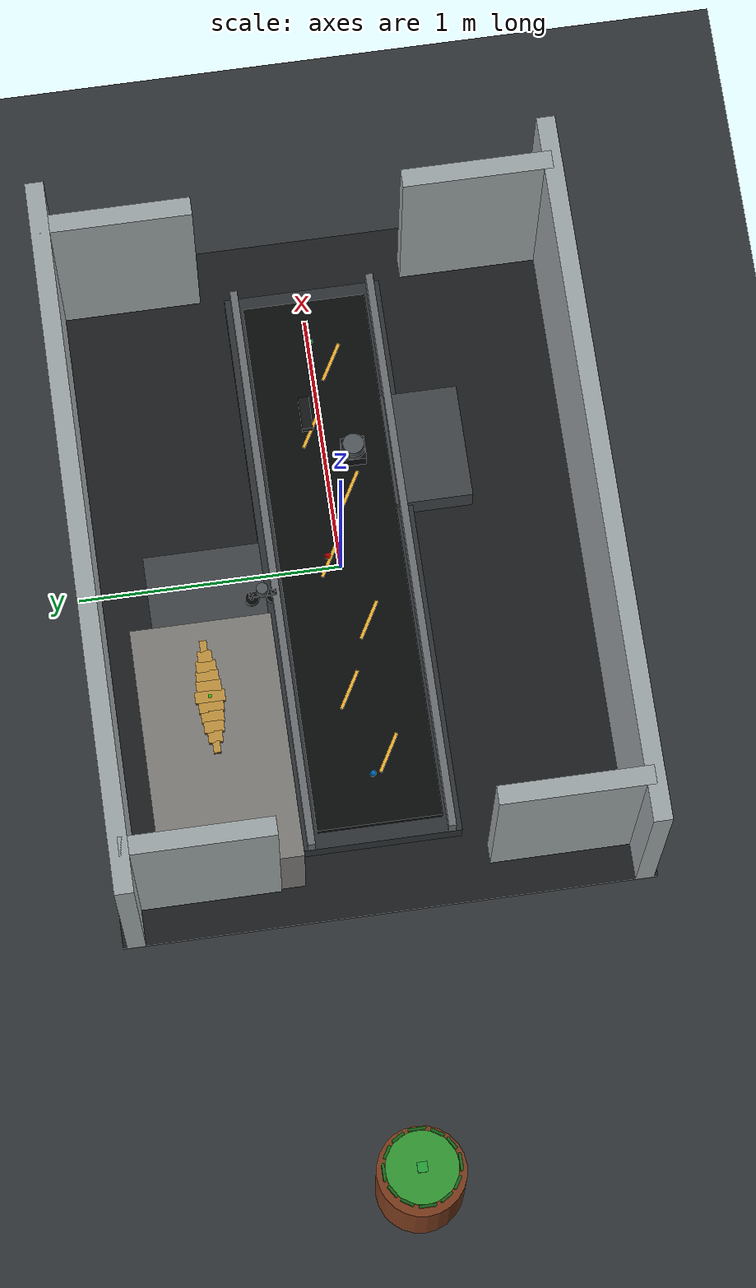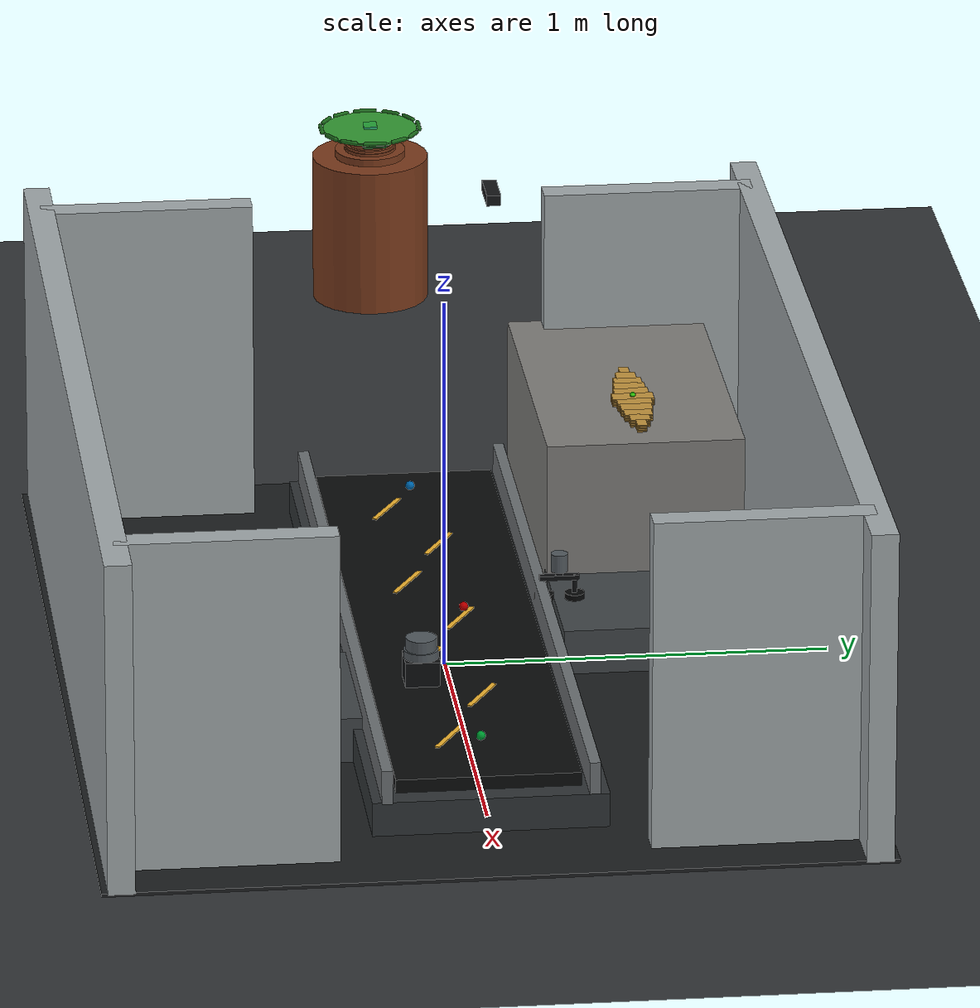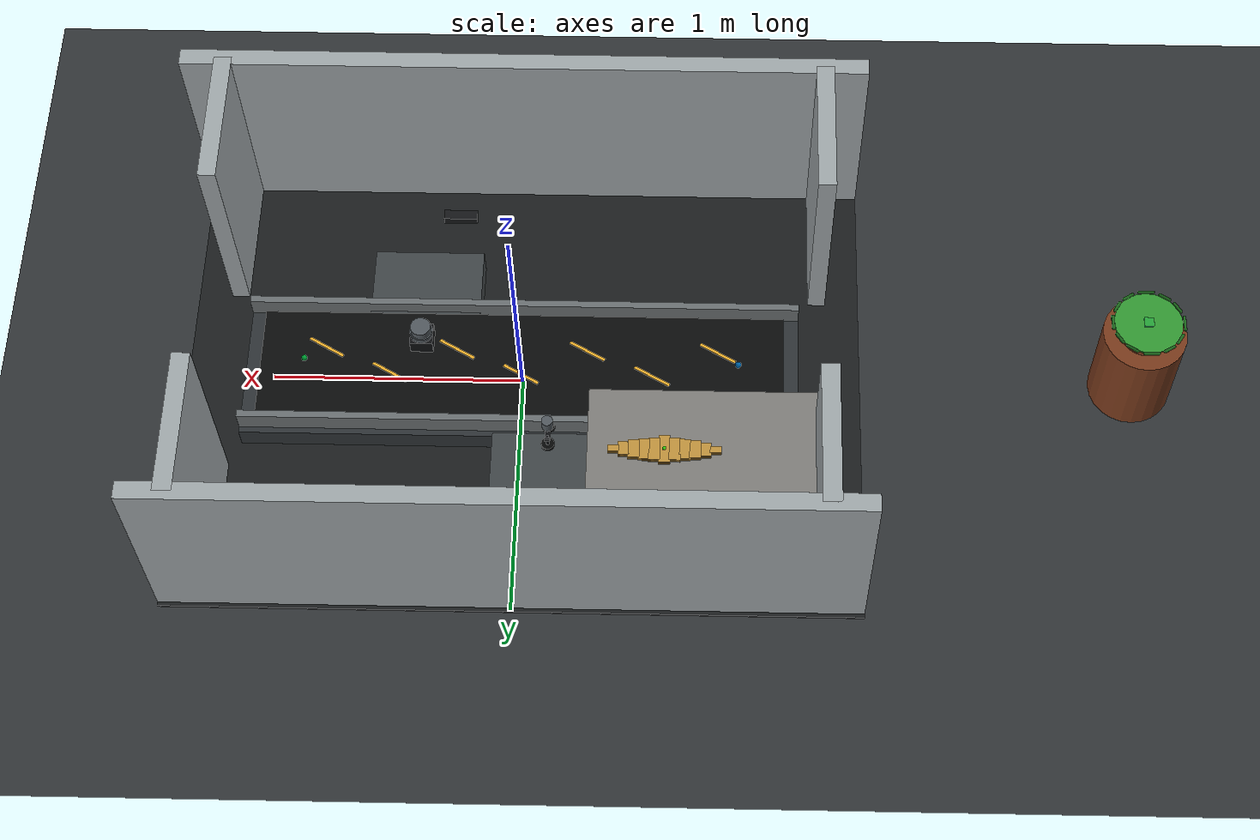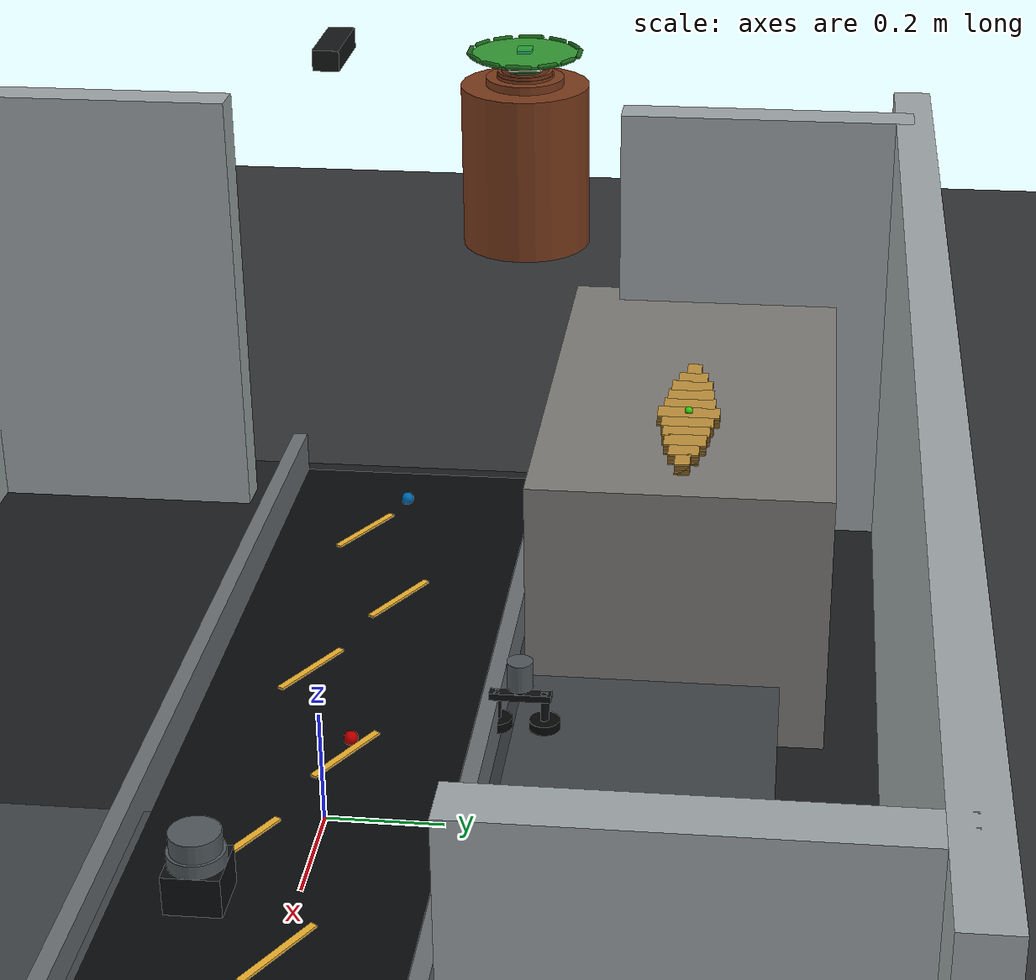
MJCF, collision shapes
<mujoco model="winejar production animation demo scene">
  <include file="xarm6_left_vacuum.xml"/>
  <include file="xarm6_right_tie_gun.xml"/>
  <include file="compliant_bamboo_leaf_pair.xml"/>
  <include file="production_line_instances.xml"/>

  <compiler angle="radian" meshdir="assets"/>

  <option integrator="implicitfast" gravity="0 0 -9.81" timestep="0.001"/>
  <statistic center="0 0 0.48" extent="1.55"/>

  <visual>
    <quality shadowsize="2048"/>
    <headlight diffuse="0.30 0.30 0.28" ambient="0.16 0.17 0.18" specular="0.18 0.18 0.16"/>
    <rgba haze="0.74 0.78 0.82 1"/>
    <global azimuth="135" elevation="-24" offwidth="1280" offheight="720"/>
  </visual>

  <asset>
    <texture type="skybox" builtin="gradient" rgb1="0.82 0.86 0.90" rgb2="0.26 0.30 0.34"
             width="512" height="3072"/>
    <texture type="2d" name="ground_texture" builtin="checker"
             rgb1="0.18 0.19 0.20" rgb2="0.21 0.22 0.23" width="512" height="512"/>
    <material name="ground_material" texture="ground_texture" texuniform="true" texrepeat="18 18"
              specular="0.08" shininess="0.12" reflectance="0.02"/>
    <material name="factory_floor_mat" texture="ground_texture" texuniform="true" texrepeat="16 12"
              rgba="0.55 0.57 0.56 1" specular="0.12" shininess="0.16" reflectance="0.03"/>
    <material name="factory_wall_mat" rgba="0.63 0.66 0.67 1" specular="0.08" shininess="0.12"/>
    <material name="factory_ceiling_mat" rgba="0.70 0.72 0.72 1" specular="0.10" shininess="0.14"/>

    <texture type="2d" name="workbench_texture" file="textures/workbench_laminate.png"/>
    <material name="workbench_mat" texture="workbench_texture" texuniform="true" texrepeat="2 2"
              rgba="0.66 0.68 0.70 1" specular="0.14" shininess="0.18" reflectance="0.02"/>
    <material name="base_mat" rgba="0.25 0.27 0.28 1" specular="0.15" shininess="0.20"/>
    <material name="conveyor_frame_mat" rgba="0.18 0.20 0.21 1" specular="0.18" shininess="0.22"/>
    <material name="conveyor_belt_mat" rgba="0.035 0.04 0.042 1" specular="0.06" shininess="0.08"/>
    <material name="conveyor_rail_mat" rgba="0.42 0.44 0.45 1" specular="0.22" shininess="0.30"/>
    <material name="belt_marker_mat" rgba="0.94 0.70 0.18 1" specular="0.10" shininess="0.12"/>
    <material name="jar_mat" rgba="0.48 0.23 0.11 1" specular="0.18" shininess="0.32"/>
    <material name="jar_collision_mat" rgba="0.48 0.23 0.11 0.10"/>
    <material name="lotus_mat" rgba="0.18 0.45 0.20 1" specular="0.08" shininess="0.15"/>
    <material name="paper_mat" rgba="0.94 0.93 0.88 1" specular="0.05" shininess="0.10"/>
    <material name="ceramic_mat" rgba="0.72 0.34 0.12 1" specular="0.18" shininess="0.28"/>
    <material name="bamboo_mat_top" rgba="0.76 0.58 0.24 1" specular="0.08" shininess="0.12"/>
    <material name="bamboo_mat_bottom" rgba="0.62 0.46 0.18 1" specular="0.08" shininess="0.12"/>
    <material name="label_mat" rgba="0.93 0.82 0.46 1" specular="0.05" shininess="0.10"/>
    <material name="camera_body_mat" rgba="0.08 0.085 0.09 1" specular="0.18" shininess="0.22"/>
    <material name="camera_lens_mat" rgba="0.01 0.012 0.014 1" specular="0.28" shininess="0.35"/>
    <material name="target_marker_mat" rgba="0.0 0.55 1.0 0.28"/>

    <mesh name="wine_jar_mesh" file="materials/wine_jar.stl"/>
    <mesh name="cropped_lotus_leaf_mesh" file="materials/cropped_lotus_leaf.stl"/>
    <mesh name="cropped_lotus_leaf_tie_safe_mesh" file="materials/cropped_lotus_leaf.stl" scale="0.70 0.70 1"/>
    <mesh name="cropped_white_paper_mesh" file="materials/cropped_white_paper.stl"/>
    <mesh name="bamboo_leaf_mesh" file="materials/bamboo_leaf.stl"/>
    <mesh name="preloaded_lotus_center_mesh" file="materials/preloaded_lotus_center.stl"/>
    <mesh name="preloaded_lotus_east_mesh" file="materials/preloaded_lotus_east.stl"/>
    <mesh name="preloaded_lotus_west_mesh" file="materials/preloaded_lotus_west.stl"/>
    <mesh name="preloaded_lotus_north_mesh" file="materials/preloaded_lotus_north.stl"/>
    <mesh name="preloaded_lotus_south_mesh" file="materials/preloaded_lotus_south.stl"/>
    <mesh name="preloaded_paper_center_mesh" file="materials/preloaded_paper_center.stl"/>
    <mesh name="preloaded_paper_east_mesh" file="materials/preloaded_paper_east.stl"/>
    <mesh name="preloaded_paper_west_mesh" file="materials/preloaded_paper_west.stl"/>
    <mesh name="preloaded_paper_north_mesh" file="materials/preloaded_paper_north.stl"/>
    <mesh name="preloaded_paper_south_mesh" file="materials/preloaded_paper_south.stl"/>
  </asset>

  <worldbody>
    <light name="key_light" pos="-0.6 -0.7 1.6" dir="0.35 0.35 -1" directional="true"
           diffuse="0.56 0.54 0.50" specular="0.22 0.21 0.19" castshadow="true"/>
    <light name="fill_light" pos="0.8 0.5 1.2" dir="-0.55 -0.25 -1" directional="true"
           diffuse="0.20 0.22 0.26" specular="0.06 0.07 0.09" castshadow="false"/>
    <geom name="floor" pos="0 0 -0.02" size="0 0 0.05" type="plane" material="ground_material"/>

    <body name="factory_shell">
      <geom name="factory_floor_slab" type="box" pos="0 0 -0.025" size="1.35 1.00 0.010"
            material="factory_floor_mat" contype="0" conaffinity="0"/>
      <geom name="factory_wall_y_positive" type="box" pos="0 0.95 0.42" size="1.35 0.035 0.44"
            material="factory_wall_mat" contype="0" conaffinity="0"/>
      <geom name="factory_wall_y_negative" type="box" pos="0 -0.95 0.42" size="1.35 0.035 0.44"
            material="factory_wall_mat" contype="0" conaffinity="0"/>
      <geom name="factory_wall_x_negative_left" type="box" pos="-1.18 -0.67 0.42" size="0.035 0.28 0.44"
            material="factory_wall_mat" contype="0" conaffinity="0"/>
      <geom name="factory_wall_x_negative_right" type="box" pos="-1.18 0.67 0.42" size="0.035 0.28 0.44"
            material="factory_wall_mat" contype="0" conaffinity="0"/>
      <geom name="factory_wall_x_positive_left" type="box" pos="1.18 -0.67 0.42" size="0.035 0.28 0.44"
            material="factory_wall_mat" contype="0" conaffinity="0"/>
      <geom name="factory_wall_x_positive_right" type="box" pos="1.18 0.67 0.42" size="0.035 0.28 0.44"
            material="factory_wall_mat" contype="0" conaffinity="0"/>
    </body>

    <body name="conveyor">
      <geom name="conveyor_frame" type="box" pos="0 0 0.045" size="1.10 0.30 0.045" material="conveyor_frame_mat"/>
      <geom name="conveyor_belt" type="box" pos="0 0 0.107" size="1.04 0.235 0.018" material="conveyor_belt_mat"/>
      <geom name="conveyor_left_rail" type="box" pos="0 0.262 0.130" size="1.10 0.014 0.045" material="conveyor_rail_mat"/>
      <geom name="conveyor_right_rail" type="box" pos="0 -0.262 0.130" size="1.10 0.014 0.045" material="conveyor_rail_mat"/>
      <geom name="belt_marker_0" type="box" pos="-0.78 -0.07 0.128" euler="0 0 -0.52" size="0.080 0.006 0.002" material="belt_marker_mat"/>
      <geom name="belt_marker_1" type="box" pos="-0.52 0.04 0.128" euler="0 0 -0.52" size="0.080 0.006 0.002" material="belt_marker_mat"/>
      <geom name="belt_marker_2" type="box" pos="-0.26 -0.07 0.128" euler="0 0 -0.52" size="0.080 0.006 0.002" material="belt_marker_mat"/>
      <geom name="belt_marker_3" type="box" pos="0.00 0.04 0.128" euler="0 0 -0.52" size="0.080 0.006 0.002" material="belt_marker_mat"/>
      <geom name="belt_marker_4" type="box" pos="0.26 -0.07 0.128" euler="0 0 -0.52" size="0.080 0.006 0.002" material="belt_marker_mat"/>
      <geom name="belt_marker_5" type="box" pos="0.52 0.04 0.128" euler="0 0 -0.52" size="0.080 0.006 0.002" material="belt_marker_mat"/>
      <geom name="belt_marker_6" type="box" pos="0.78 -0.07 0.128" euler="0 0 -0.52" size="0.080 0.006 0.002" material="belt_marker_mat"/>
      <site name="conveyor_entry_site" pos="-0.86 0 0.16" type="sphere" size="0.012" rgba="0 0.6 1 0.7"/>
      <site name="conveyor_stop_site" pos="0 0.05 0.16" type="sphere" size="0.012" rgba="1 0 0 0.75"/>
      <site name="conveyor_exit_site" pos="0.86 0 0.16" type="sphere" size="0.012" rgba="0 0.9 0.3 0.7"/>
    </body>

    <body name="station_wine_jar" pos="-2.40 0.05 0.125">
      <geom name="wine_jar_visual" type="mesh" mesh="wine_jar_mesh" material="jar_mat" contype="0" conaffinity="0"/>
      <geom name="wine_jar_belly_collision" type="cylinder" pos="0 0 0.205" size="0.16 0.205"
            material="jar_collision_mat" mass="8" friction="1 1 1" contype="2" conaffinity="1"/>
      <geom name="wine_jar_shoulder_lower_collision" type="cylinder" pos="0 0 0.420" size="0.097 0.010"
            material="jar_collision_mat" mass="1" friction="1 1 1" contype="2" conaffinity="1"/>
      <geom name="wine_jar_shoulder_middle_collision" type="cylinder" pos="0 0 0.43375" size="0.071 0.00375"
            material="jar_collision_mat" mass="0.5" friction="1 1 1" contype="2" conaffinity="1"/>
      <geom name="wine_jar_shoulder_upper_collision" type="cylinder" pos="0 0 0.44125" size="0.068 0.00375"
            material="jar_collision_mat" mass="0.5" friction="1 1 1" contype="2" conaffinity="1"/>
      <geom name="wine_jar_neck_collision" type="cylinder" pos="0 0 0.4525" size="0.06 0.0075"
            material="jar_collision_mat" mass="1" friction="1 1 1" contype="2" conaffinity="1"/>
      <site name="jar_mouth_center" pos="0 0 0.46" type="sphere" size="0.012" rgba="1 0 0 0.8"/>
      <body name="preloaded_lotus_leaf" pos="0 0 0.462" euler="0 0 0.15">
        <geom name="preloaded_lotus_leaf_geom" type="mesh" mesh="preloaded_lotus_center_mesh" material="lotus_mat"
              mass="0.008" friction="2 1 1" contype="4" conaffinity="5"/>
        <body name="preloaded_lotus_east_flap" pos="0.044 0 0">
          <joint name="preloaded_lotus_fold_east" type="hinge" axis="0 1 0" range="0 1.57" limited="true" damping="0.01"/>
          <geom name="preloaded_lotus_east_flap_geom" type="mesh" mesh="preloaded_lotus_east_mesh" material="lotus_mat" mass="0.003" friction="2 1 1" contype="4" conaffinity="5"/>
        </body>
        <body name="preloaded_lotus_west_flap" pos="-0.044 0 0">
          <joint name="preloaded_lotus_fold_west" type="hinge" axis="0 -1 0" range="0 1.57" limited="true" damping="0.01"/>
          <geom name="preloaded_lotus_west_flap_geom" type="mesh" mesh="preloaded_lotus_west_mesh" material="lotus_mat" mass="0.003" friction="2 1 1" contype="4" conaffinity="5"/>
        </body>
        <body name="preloaded_lotus_north_flap" pos="0 0.044 0">
          <joint name="preloaded_lotus_fold_north" type="hinge" axis="-1 0 0" range="0 1.57" limited="true" damping="0.01"/>
          <geom name="preloaded_lotus_north_flap_geom" type="mesh" mesh="preloaded_lotus_north_mesh" material="lotus_mat" mass="0.002" friction="2 1 1" contype="4" conaffinity="5"/>
        </body>
        <body name="preloaded_lotus_south_flap" pos="0 -0.044 0">
          <joint name="preloaded_lotus_fold_south" type="hinge" axis="1 0 0" range="0 1.57" limited="true" damping="0.01"/>
          <geom name="preloaded_lotus_south_flap_geom" type="mesh" mesh="preloaded_lotus_south_mesh" material="lotus_mat" mass="0.002" friction="2 1 1" contype="4" conaffinity="5"/>
        </body>
      </body>
      <body name="preloaded_white_paper" pos="0 0 0.467" euler="0 0 0.15">
        <geom name="preloaded_white_paper_geom" type="mesh" mesh="preloaded_paper_center_mesh" material="paper_mat"
              mass="0.004" friction="2 1 1" contype="4" conaffinity="5"/>
        <body name="preloaded_paper_east_flap" pos="0.048 0 0">
          <joint name="preloaded_paper_fold_east" type="hinge" axis="0 1 0" range="0 1.57" limited="true" damping="0.008"/>
          <geom name="preloaded_paper_east_flap_geom" type="mesh" mesh="preloaded_paper_east_mesh" material="paper_mat" mass="0.0015" friction="2 1 1" contype="4" conaffinity="5"/>
        </body>
        <body name="preloaded_paper_west_flap" pos="-0.048 0 0">
          <joint name="preloaded_paper_fold_west" type="hinge" axis="0 -1 0" range="0 1.57" limited="true" damping="0.008"/>
          <geom name="preloaded_paper_west_flap_geom" type="mesh" mesh="preloaded_paper_west_mesh" material="paper_mat" mass="0.0015" friction="2 1 1" contype="4" conaffinity="5"/>
        </body>
        <body name="preloaded_paper_north_flap" pos="0 0.048 0">
          <joint name="preloaded_paper_fold_north" type="hinge" axis="-1 0 0" range="0 1.57" limited="true" damping="0.008"/>
          <geom name="preloaded_paper_north_flap_geom" type="mesh" mesh="preloaded_paper_north_mesh" material="paper_mat" mass="0.001" friction="2 1 1" contype="4" conaffinity="5"/>
        </body>
        <body name="preloaded_paper_south_flap" pos="0 -0.048 0">
          <joint name="preloaded_paper_fold_south" type="hinge" axis="1 0 0" range="0 1.57" limited="true" damping="0.008"/>
          <geom name="preloaded_paper_south_flap_geom" type="mesh" mesh="preloaded_paper_south_mesh" material="paper_mat" mass="0.001" friction="2 1 1" contype="4" conaffinity="5"/>
        </body>
      </body>
      <body name="preloaded_ceramic_disc" pos="0 0 0.476">
        <geom name="preloaded_ceramic_disc_geom" type="cylinder" size="0.055 0.006" material="ceramic_mat"
              mass="0.20" friction="1 1 1"/>
        <site name="ceramic_disc_center_site" pos="0 0 0.007" type="sphere" size="0.007" rgba="1 0 0 0.6"/>
      </body>
      <geom name="mouth_material_support_collision" type="cylinder" pos="0 0 0.485"
            size="0.130 0.003" rgba="0.2 0.6 0.2 0.0" mass="0.02"
            friction="8.0 3.0 2.0" condim="6" contype="2" conaffinity="1"/>
      <body name="mouth_material_retaining_lip" pos="0 0 0.491">
        <geom name="mouth_material_lip_00" type="capsule" fromto="0.1350 -0.0268 0 0.1350 0.0268 0" size="0.006"
              rgba="0.1 0.4 0.1 0.0" friction="8.0 3.0 2.0" condim="6" contype="2" conaffinity="1"/>
        <geom name="mouth_material_lip_01" type="capsule" fromto="0.1247 0.0517 0 0.1032 0.0865 0" size="0.006"
              rgba="0.1 0.4 0.1 0.0" friction="8.0 3.0 2.0" condim="6" contype="2" conaffinity="1"/>
        <geom name="mouth_material_lip_02" type="capsule" fromto="0.0865 0.1032 0 0.0517 0.1247 0" size="0.006"
              rgba="0.1 0.4 0.1 0.0" friction="8.0 3.0 2.0" condim="6" contype="2" conaffinity="1"/>
        <geom name="mouth_material_lip_03" type="capsule" fromto="0.0268 0.1350 0 -0.0268 0.1350 0" size="0.006"
              rgba="0.1 0.4 0.1 0.0" friction="8.0 3.0 2.0" condim="6" contype="2" conaffinity="1"/>
        <geom name="mouth_material_lip_04" type="capsule" fromto="-0.0517 0.1247 0 -0.0865 0.1032 0" size="0.006"
              rgba="0.1 0.4 0.1 0.0" friction="8.0 3.0 2.0" condim="6" contype="2" conaffinity="1"/>
        <geom name="mouth_material_lip_05" type="capsule" fromto="-0.1032 0.0865 0 -0.1247 0.0517 0" size="0.006"
              rgba="0.1 0.4 0.1 0.0" friction="8.0 3.0 2.0" condim="6" contype="2" conaffinity="1"/>
        <geom name="mouth_material_lip_06" type="capsule" fromto="-0.1350 0.0268 0 -0.1350 -0.0268 0" size="0.006"
              rgba="0.1 0.4 0.1 0.0" friction="8.0 3.0 2.0" condim="6" contype="2" conaffinity="1"/>
        <geom name="mouth_material_lip_07" type="capsule" fromto="-0.1247 -0.0517 0 -0.1032 -0.0865 0" size="0.006"
              rgba="0.1 0.4 0.1 0.0" friction="8.0 3.0 2.0" condim="6" contype="2" conaffinity="1"/>
        <geom name="mouth_material_lip_08" type="capsule" fromto="-0.0865 -0.1032 0 -0.0517 -0.1247 0" size="0.006"
              rgba="0.1 0.4 0.1 0.0" friction="8.0 3.0 2.0" condim="6" contype="2" conaffinity="1"/>
        <geom name="mouth_material_lip_09" type="capsule" fromto="-0.0268 -0.1350 0 0.0268 -0.1350 0" size="0.006"
              rgba="0.1 0.4 0.1 0.0" friction="8.0 3.0 2.0" condim="6" contype="2" conaffinity="1"/>
        <geom name="mouth_material_lip_10" type="capsule" fromto="0.0517 -0.1247 0 0.0865 -0.1032 0" size="0.006"
              rgba="0.1 0.4 0.1 0.0" friction="8.0 3.0 2.0" condim="6" contype="2" conaffinity="1"/>
        <geom name="mouth_material_lip_11" type="capsule" fromto="0.1032 -0.0865 0 0.1247 -0.0517 0" size="0.006"
              rgba="0.1 0.4 0.1 0.0" friction="8.0 3.0 2.0" condim="6" contype="2" conaffinity="1"/>
      </body>
      <site name="leaf_cross_target_0" pos="0 0 0.494" euler="0 0 0" type="box" size="0.018 0.018 0.002"
            material="target_marker_mat"/>
      <site name="leaf_cross_target_90" pos="0 0 0.500" euler="0 0 1.5708" type="box" size="0.018 0.018 0.002"
            rgba="0 0.85 0.35 0.22"/>
      <site name="neck_tie_target_site" pos="0 0 0.452" type="sphere" size="0.012" rgba="0 0.7 1 0.75"/>
      <body name="final_tie_band_visual" pos="0 0 0.455">
        <geom name="final_tie_band_visual_geom_00" type="capsule" fromto="0.0630 -0.0063 0 0.0630 0.0063 0" size="0.0035"
              rgba="0.02 0.02 0.02 0.0" contype="0" conaffinity="0"/>
        <geom name="final_tie_band_visual_geom_01" type="capsule" fromto="0.0606 0.0185 0 0.0558 0.0301 0" size="0.0035"
              rgba="0.02 0.02 0.02 0.0" contype="0" conaffinity="0"/>
        <geom name="final_tie_band_visual_geom_02" type="capsule" fromto="0.0490 0.0401 0 0.0401 0.0490 0" size="0.0035"
              rgba="0.02 0.02 0.02 0.0" contype="0" conaffinity="0"/>
        <geom name="final_tie_band_visual_geom_03" type="capsule" fromto="0.0301 0.0558 0 0.0185 0.0606 0" size="0.0035"
              rgba="0.02 0.02 0.02 0.0" contype="0" conaffinity="0"/>
        <geom name="final_tie_band_visual_geom_04" type="capsule" fromto="0.0063 0.0630 0 -0.0063 0.0630 0" size="0.0035"
              rgba="0.02 0.02 0.02 0.0" contype="0" conaffinity="0"/>
        <geom name="final_tie_band_visual_geom_05" type="capsule" fromto="-0.0185 0.0606 0 -0.0301 0.0558 0" size="0.0035"
              rgba="0.02 0.02 0.02 0.0" contype="0" conaffinity="0"/>
        <geom name="final_tie_band_visual_geom_06" type="capsule" fromto="-0.0401 0.0490 0 -0.0490 0.0401 0" size="0.0035"
              rgba="0.02 0.02 0.02 0.0" contype="0" conaffinity="0"/>
        <geom name="final_tie_band_visual_geom_07" type="capsule" fromto="-0.0558 0.0301 0 -0.0606 0.0185 0" size="0.0035"
              rgba="0.02 0.02 0.02 0.0" contype="0" conaffinity="0"/>
        <geom name="final_tie_band_visual_geom_08" type="capsule" fromto="-0.0630 0.0063 0 -0.0630 -0.0063 0" size="0.0035"
              rgba="0.02 0.02 0.02 0.0" contype="0" conaffinity="0"/>
        <geom name="final_tie_band_visual_geom_09" type="capsule" fromto="-0.0606 -0.0185 0 -0.0558 -0.0301 0" size="0.0035"
              rgba="0.02 0.02 0.02 0.0" contype="0" conaffinity="0"/>
        <geom name="final_tie_band_visual_geom_10" type="capsule" fromto="-0.0490 -0.0401 0 -0.0401 -0.0490 0" size="0.0035"
              rgba="0.02 0.02 0.02 0.0" contype="0" conaffinity="0"/>
        <geom name="final_tie_band_visual_geom_11" type="capsule" fromto="-0.0301 -0.0558 0 -0.0185 -0.0606 0" size="0.0035"
              rgba="0.02 0.02 0.02 0.0" contype="0" conaffinity="0"/>
        <geom name="final_tie_band_visual_geom_12" type="capsule" fromto="-0.0063 -0.0630 0 0.0063 -0.0630 0" size="0.0035"
              rgba="0.02 0.02 0.02 0.0" contype="0" conaffinity="0"/>
        <geom name="final_tie_band_visual_geom_13" type="capsule" fromto="0.0185 -0.0606 0 0.0301 -0.0558 0" size="0.0035"
              rgba="0.02 0.02 0.02 0.0" contype="0" conaffinity="0"/>
        <geom name="final_tie_band_visual_geom_14" type="capsule" fromto="0.0401 -0.0490 0 0.0490 -0.0401 0" size="0.0035"
              rgba="0.02 0.02 0.02 0.0" contype="0" conaffinity="0"/>
        <geom name="final_tie_band_visual_geom_15" type="capsule" fromto="0.0558 -0.0301 0 0.0606 -0.0185 0" size="0.0035"
              rgba="0.02 0.02 0.02 0.0" contype="0" conaffinity="0"/>
      </body>
    </body>

    <body name="left_robot_pedestal" pos="-0.12 0.52 0.06">
      <geom name="left_robot_pedestal_geom" type="box" size="0.22 0.22 0.06" material="base_mat"
            mass="2000" friction="1 1 1"/>
    </body>
    <body name="right_robot_pedestal" pos="0.40 -0.31 0.06">
      <geom name="right_robot_pedestal_geom" type="box" size="0.22 0.22 0.06" material="base_mat"
            mass="2000" friction="1 1 1"/>
    </body>

    <body name="left_material_table" pos="-0.75 0.56 0.24">
      <geom name="left_material_table_geom" type="box" size="0.46 0.26 0.24" material="workbench_mat"
            mass="2000" friction="1 1 1"/>
    </body>
    <body name="global_camera_rig" pos="0.14 0.105 1.35">
      <geom name="global_camera_body_geom" type="box" pos="0 0 0" size="0.058 0.018 0.014"
            material="camera_body_mat" mass="0.4" contype="0" conaffinity="0"/>
      <geom name="global_camera_left_lens_geom" type="cylinder" pos="-0.025 0 -0.018" size="0.007 0.004"
            material="camera_lens_mat" mass="0.02" contype="0" conaffinity="0"/>
      <geom name="global_camera_right_lens_geom" type="cylinder" pos="0.025 0 -0.018" size="0.007 0.004"
            material="camera_lens_mat" mass="0.02" contype="0" conaffinity="0"/>
      <camera name="global_top_camera" pos="0 0 -0.02" xyaxes="1 0 0 0 1 0" fovy="48" resolution="1280 720"/>
    </body>

    <camera name="global_overview_camera" pos="0.05 -0.10 2.05"
            xyaxes="0.96352 0.26764 0.00000 -0.26617 0.95820 0.10496"
            fovy="62" resolution="1280 720"/>
    <camera name="front_conveyor_camera" pos="1.75 0.05 0.70"
            xyaxes="0.00000 1.00000 0.00000 -0.17987 0.00000 0.98369"
            fovy="52" resolution="1280 720"/>
    <camera name="side_overview_camera" pos="1.31250 -0.98452 1.50000"
            xyaxes="0.64461 0.76451 0.00000 -0.40459 0.34114 0.84849"
            fovy="45" resolution="1280 720"/>
    <camera name="production_hero_camera" pos="1.25 -1.05 0.86" xyaxes="0.68 0.73 0 -0.28 0.26 0.92" fovy="42" resolution="1920 1080"/>
    <camera name="jar_mouth_closeup_camera" pos="0.38 -0.45 0.76" xyaxes="0.75 0.66 0 -0.36 0.41 0.84" fovy="32" resolution="1280 720"/>
    <camera name="left_vacuum_closeup_camera" pos="-0.52 0.98 0.86" xyaxes="-0.72 0.69 0 -0.33 -0.35 0.88" fovy="36" resolution="1280 720"/>
    <camera name="right_tie_gun_closeup_camera" pos="-0.52 -0.70 0.78" xyaxes="0.82 -0.57 0 0.28 0.40 0.87" fovy="34" resolution="1280 720"/>
  </worldbody>

  <equality>
    <weld name="left_suction_weld_leaf_top" body1="left_vacuum_end_effector" body2="staged_bamboo_leaf_top_seg_05"
          active="false" solref="0.004 1" solimp="0.95 0.99 0.001"/>
    <weld name="left_suction_weld_leaf_bottom" body1="left_vacuum_end_effector" body2="staged_bamboo_leaf_bottom_seg_05"
          active="false" solref="0.004 1" solimp="0.95 0.99 0.001"/>
    <weld name="table_static_friction_weld_leaf_top" body1="left_material_table" body2="staged_bamboo_leaf_top_seg_05"
          active="false" solref="0.030 1" solimp="0.70 0.95 0.010"/>
    <weld name="table_static_friction_weld_leaf_bottom" body1="left_material_table" body2="staged_bamboo_leaf_bottom_seg_05"
          active="false" solref="0.030 1" solimp="0.70 0.95 0.010"/>
    <weld name="mouth_static_friction_weld_leaf_top" body1="station_wine_jar" body2="staged_bamboo_leaf_top_seg_05"
          active="false" solref="0.030 1" solimp="0.70 0.95 0.010"/>
    <weld name="mouth_static_friction_weld_leaf_bottom" body1="station_wine_jar" body2="staged_bamboo_leaf_bottom_seg_05"
          active="false" solref="0.030 1" solimp="0.70 0.95 0.010"/>
  </equality>
</mujoco>

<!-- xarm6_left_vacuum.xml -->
<mujoco model="left xarm6">
  <compiler angle="radian" autolimits="true" meshdir="assets" />
  <option integrator="implicitfast" gravity="0 0 -9.81" />
  <asset>
    <material name="left_white" rgba="0.86 0.88 0.89 1" specular="0.32" shininess="0.42" reflectance="0.04" />
    <material name="left_gray" rgba="0.32 0.35 0.37 1" specular="0.55" shininess="0.62" reflectance="0.10" />
    <material name="left_black" rgba="0.045 0.052 0.058 1" specular="0.16" shininess="0.24" reflectance="0.02" />
    <material name="left_vacuum_rubber" rgba="0.02 0.025 0.025 1" specular="0.06" shininess="0.12" />
    <mesh file="link_base.stl" name="left_link_base" />
    <mesh file="link1.stl" name="left_link1" />
    <mesh file="link2.stl" name="left_link2" />
    <mesh file="link3.stl" name="left_link3" />
    <mesh file="link4.stl" name="left_link4" />
    <mesh file="link5.stl" name="left_link5" />
    <mesh file="link6.stl" name="left_link6" />
    <mesh file="end_tool.stl" name="left_end_tool" />
  </asset>
  <default>
    <default class="left_xarm6">
      <geom type="mesh" material="left_white" contype="0" conaffinity="0" />
      <joint axis="0 0 1" armature="0.1" range="-6.28319 6.28319" frictionloss="1" />
      <default class="left_size1">
        <joint damping="10" />
      </default>
      <default class="left_size2">
        <joint damping="5" />
      </default>
      <default class="left_size3">
        <joint damping="2" />
      </default>
      <default class="left_visual">
        <geom type="mesh" contype="0" conaffinity="0" group="2" />
      </default>
      <site size="0.001" rgba="1 0 0 1" group="4" />
    </default>
  </default>
  <worldbody>
    <body name="left_line_base" pos="-0.12 0.52 0.12" childclass="left_xarm6" euler="0 0 -1.5708">
      <inertial pos="-0.021131 -0.0016302 0.056488" quat="0.696843 0.20176 0.10388 0.680376" mass="0.88556" diaginertia="0.00382023 0.00335282 0.00167725" />
      <geom mesh="left_link_base" />
      <body name="left_link1" pos="0 0 0.267">
        <inertial pos="-0.0002 0.02905 -0.01233" quat="0.978953 -0.202769 -0.00441617 -0.0227264" mass="2.382" diaginertia="0.00569127 0.00533384 0.00293865" />
        <joint name="left_joint1" class="left_size1" />
        <geom mesh="left_link1" />
        <body name="left_link2" quat="1 -1 0 0">
          <inertial pos="0.03881 -0.22783 0.03496" quat="0.635305 0.753023 0.170976 -0.010531" mass="2.2675" diaginertia="0.0294477 0.0281783 0.00383449" />
          <joint name="left_joint2" range="-2.059 2.0944" class="left_size1" />
          <geom mesh="left_link2" />
          <body name="left_link3" pos="0.0535 -0.2845 0">
            <inertial pos="0.07041 0.11631 0.0107" quat="0.845838 0.425539 -0.293179 0.132369" mass="1.875" diaginertia="0.00714132 0.00699471 0.00196753" />
            <joint name="left_joint3" range="-3.927 0.19198" class="left_size2" />
            <geom mesh="left_link3" />
            <body name="left_link4" pos="0.0775 0.3425 0" quat="1 -1 0 0">
              <inertial pos="-0.00018 0.01798 -0.02291" quat="0.99929 -0.0369702 0.00179434 -0.00701174" mass="1.3192" diaginertia="0.00489614 0.00447403 0.00132609" />
              <joint name="left_joint4" class="left_size2" />
              <geom mesh="left_link4" />
              <body name="left_link5" pos="0 0 0" quat="1 1 0 0">
                <inertial pos="0.0651 0.03096 0.00315" quat="-0.223008 0.771309 0.16027 0.574163" mass="1.33854" diaginertia="0.00241824 0.00213367 0.00108731" />
                <joint name="left_joint5" range="-1.69297 3.14159" class="left_size3" />
                <geom mesh="left_link5" />
                <body name="left_link6" pos="0.076 0.097 0" quat="1 -1 0 0">
                  <inertial pos="0.00763576 -0.00272358 0.0307029" quat="0.634077 -0.153028 -0.073538 0.754401" mass="0.838615" diaginertia="0.00129456 0.00116006 0.00078716" />
                  <joint name="left_joint6" class="left_size3" />
                  <geom material="left_gray" mesh="left_end_tool" quat="0 0 0 1" />
                  <body name="left_vacuum_end_effector" pos="0 0 0.015">
                    <inertial pos="0 0 0.045" mass="0.25" diaginertia="0.00018 0.00018 0.00008" />
                    <geom name="left_vacuum_mount_geom" type="cylinder" pos="0 0 -0.008" size="0.022 0.024" material="left_gray" mass="0.12" friction="0.8 0.8 0.8" contype="0" conaffinity="0" />
                    <geom name="left_vacuum_center_connector_geom" type="cylinder" pos="0 0 0.022" size="0.010 0.014" material="left_black" mass="0.025" friction="0.8 0.8 0.8" contype="0" conaffinity="0" />
                    <geom name="left_vacuum_crossbar_geom" type="box" pos="0 0 0.034" size="0.052 0.010 0.006" material="left_black" mass="0.04" friction="0.8 0.8 0.8" contype="0" conaffinity="0" />
                    <geom name="left_vacuum_stem_left_geom" type="cylinder" pos="-0.040 0 0.054" size="0.007 0.026" material="left_black" mass="0.025" friction="0.8 0.8 0.8" contype="0" conaffinity="0" />
                    <geom name="left_vacuum_stem_right_geom" type="cylinder" pos="0.040 0 0.054" size="0.007 0.026" material="left_black" mass="0.025" friction="0.8 0.8 0.8" contype="0" conaffinity="0" />
                    <geom name="left_vacuum_cup_left_geom" type="cylinder" pos="-0.040 0 0.086" size="0.026 0.008" material="left_vacuum_rubber" mass="0.04" friction="1.2 1.2 1.2" contype="0" conaffinity="0" />
                    <geom name="left_vacuum_cup_right_geom" type="cylinder" pos="0.040 0 0.086" size="0.026 0.008" material="left_vacuum_rubber" mass="0.04" friction="1.2 1.2 1.2" contype="0" conaffinity="0" />
                    <site name="left_vacuum_suction_site" pos="0 0 0.087" type="sphere" size="0.008" rgba="0 0.8 1 0.85" />
                    <site name="left_link_tcp" pos="0 0 0.087" type="sphere" size="0.01" rgba="1 0 0 0" group="1" />
                  </body>
                </body>
              </body>
            </body>
          </body>
        </body>
      </body>
    </body>
  </worldbody>
  <actuator>
    <velocity name="left_vel1" joint="left_joint1" kv="1000" ctrlrange="-3.14159 3.14159" forcerange="-50 50" />
    <velocity name="left_vel2" joint="left_joint2" kv="1000" ctrlrange="-3.14159 3.14159" forcerange="-50 50" />
    <velocity name="left_vel3" joint="left_joint3" kv="1000" ctrlrange="-3.14159 3.14159" forcerange="-30 30" />
    <velocity name="left_vel4" joint="left_joint4" kv="1000" ctrlrange="-3.14159 3.14159" forcerange="-30 30" />
    <velocity name="left_vel5" joint="left_joint5" kv="1000" ctrlrange="-3.14159 3.14159" forcerange="-20 20" />
    <velocity name="left_vel6" joint="left_joint6" kv="1000" ctrlrange="-3.14159 3.14159" forcerange="-20 20" />
  </actuator>
</mujoco>

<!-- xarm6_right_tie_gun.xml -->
<mujoco model="right xarm6">
  <compiler angle="radian" autolimits="true" meshdir="assets" />
  <option integrator="implicitfast" gravity="0 0 -9.81" />
  <asset>
    <material name="right_white" rgba="0.86 0.88 0.89 1" specular="0.32" shininess="0.42" reflectance="0.04" />
    <material name="right_gray" rgba="0.32 0.35 0.37 1" specular="0.55" shininess="0.62" reflectance="0.10" />
    <material name="right_black" rgba="0.045 0.052 0.058 1" specular="0.16" shininess="0.24" reflectance="0.02" />
    <material name="right_vacuum_rubber" rgba="0.02 0.025 0.025 1" specular="0.06" shininess="0.12" />
    <mesh file="link_base.stl" name="right_link_base" />
    <mesh file="link1.stl" name="right_link1" />
    <mesh file="link2.stl" name="right_link2" />
    <mesh file="link3.stl" name="right_link3" />
    <mesh file="link4.stl" name="right_link4" />
    <mesh file="link5.stl" name="right_link5" />
    <mesh file="link6.stl" name="right_link6" />
    <mesh file="end_tool.stl" name="right_end_tool" />
  </asset>
  <default>
    <default class="right_xarm6">
      <geom type="mesh" material="right_white" contype="0" conaffinity="0" />
      <joint axis="0 0 1" armature="0.1" range="-6.28319 6.28319" frictionloss="1" />
      <default class="right_size1">
        <joint damping="10" />
      </default>
      <default class="right_size2">
        <joint damping="5" />
      </default>
      <default class="right_size3">
        <joint damping="2" />
      </default>
      <default class="right_visual">
        <geom type="mesh" contype="0" conaffinity="0" group="2" />
      </default>
      <site size="0.001" rgba="1 0 0 1" group="4" />
    </default>
  </default>
  <worldbody>
    <body name="right_line_base" pos="0.40 -0.31 0.12" childclass="right_xarm6" euler="0 0 1.5708">
      <inertial pos="-0.021131 -0.0016302 0.056488" quat="0.696843 0.20176 0.10388 0.680376" mass="0.88556" diaginertia="0.00382023 0.00335282 0.00167725" />
      <geom mesh="right_link_base" />
      <body name="right_link1" pos="0 0 0.267">
        <inertial pos="-0.0002 0.02905 -0.01233" quat="0.978953 -0.202769 -0.00441617 -0.0227264" mass="2.382" diaginertia="0.00569127 0.00533384 0.00293865" />
        <joint name="right_joint1" class="right_size1" />
        <geom mesh="right_link1" />
        <body name="right_link2" quat="1 -1 0 0">
          <inertial pos="0.03881 -0.22783 0.03496" quat="0.635305 0.753023 0.170976 -0.010531" mass="2.2675" diaginertia="0.0294477 0.0281783 0.00383449" />
          <joint name="right_joint2" range="-2.059 2.0944" class="right_size1" />
          <geom mesh="right_link2" />
          <body name="right_link3" pos="0.0535 -0.2845 0">
            <inertial pos="0.07041 0.11631 0.0107" quat="0.845838 0.425539 -0.293179 0.132369" mass="1.875" diaginertia="0.00714132 0.00699471 0.00196753" />
            <joint name="right_joint3" range="-3.927 0.19198" class="right_size2" />
            <geom mesh="right_link3" />
            <body name="right_link4" pos="0.0775 0.3425 0" quat="1 -1 0 0">
              <inertial pos="-0.00018 0.01798 -0.02291" quat="0.99929 -0.0369702 0.00179434 -0.00701174" mass="1.3192" diaginertia="0.00489614 0.00447403 0.00132609" />
              <joint name="right_joint4" class="right_size2" />
              <geom mesh="right_link4" />
              <body name="right_link5" pos="0 0 0" quat="1 1 0 0">
                <inertial pos="0.0651 0.03096 0.00315" quat="-0.223008 0.771309 0.16027 0.574163" mass="1.33854" diaginertia="0.00241824 0.00213367 0.00108731" />
                <joint name="right_joint5" range="-1.69297 3.14159" class="right_size3" />
                <geom mesh="right_link5" />
                <body name="right_link6" pos="0.076 0.097 0" quat="1 -1 0 0">
                  <inertial pos="0.00763576 -0.00272358 0.0307029" quat="0.634077 -0.153028 -0.073538 0.754401" mass="0.838615" diaginertia="0.00129456 0.00116006 0.00078716" />
                  <joint name="right_joint6" class="right_size3" />
                  <geom material="right_gray" mesh="right_end_tool" quat="0 0 0 1" />
                  <body name="right_tie_gun_end_effector" pos="0 0 0.015">
                    <inertial pos="0 0 0.085" mass="0.45" diaginertia="0.00035 0.00035 0.00018" />
                    <geom name="right_tie_gun_flange_socket" type="cylinder" pos="0 0 -0.008" size="0.040 0.020" material="right_gray" mass="0.08" friction="0.8 0.8 0.8" contype="4" conaffinity="1" />
                    <geom name="right_tie_gun_wrist_flange" type="cylinder" pos="0 0 0.016" size="0.045 0.012" material="right_gray" mass="0.08" friction="0.8 0.8 0.8" contype="4" conaffinity="1" />
                    <geom name="right_tie_gun_body" type="box" pos="0 0 0.076" size="0.045 0.045 0.050" material="right_black" mass="0.24" friction="0.8 0.8 0.8" contype="4" conaffinity="1" />
                    <geom name="right_tie_gun_press_spring_0" type="capsule" fromto="-0.010 0 0.126 0.010 0 0.138625" size="0.0025" material="right_gray" contype="0" conaffinity="0" />
                    <geom name="right_tie_gun_press_spring_1" type="capsule" fromto="0.010 0 0.138625 -0.010 0 0.151250" size="0.0025" material="right_gray" contype="0" conaffinity="0" />
                    <geom name="right_tie_gun_press_spring_2" type="capsule" fromto="-0.010 0 0.151250 0.010 0 0.163875" size="0.0025" material="right_gray" contype="0" conaffinity="0" />
                    <geom name="right_tie_gun_press_spring_3" type="capsule" fromto="0.010 0 0.163875 0.000 0 0.176500" size="0.0025" material="right_gray" contype="0" conaffinity="0" />
                    <geom name="right_tie_gun_press_ball" type="sphere" pos="0 0 0.1925" size="0.016" material="right_gray" mass="0.03" friction="1.2 1.0 0.4" condim="6" contype="4" conaffinity="1" />
                    <geom name="right_tie_gun_support_rod_front" type="capsule" fromto="0.000 0.036 0.126 0.000 0.088 0.196" size="0.007" material="right_black" mass="0.02" friction="0.8 0.8 0.8" contype="4" conaffinity="1" />
                    <geom name="right_tie_gun_support_rod_back" type="capsule" fromto="0.000 -0.036 0.126 0.000 -0.088 0.196" size="0.007" material="right_black" mass="0.02" friction="0.8 0.8 0.8" contype="4" conaffinity="1" />
                    <geom name="right_tie_gun_support_rod_left" type="capsule" fromto="-0.036 0.000 0.126 -0.088 0.000 0.196" size="0.007" material="right_black" mass="0.02" friction="0.8 0.8 0.8" contype="4" conaffinity="1" />
                    <geom name="right_tie_gun_support_rod_right" type="capsule" fromto="0.036 0.000 0.126 0.088 0.000 0.196" size="0.007" material="right_black" mass="0.02" friction="0.8 0.8 0.8" contype="4" conaffinity="1" />
                    <geom name="right_tie_gun_left_open_jaw_0" type="capsule" fromto="0.09867 0.03591 0.20200 0.08043 0.06749 0.20200" size="0.00600" material="right_black" mass="0.01" friction="0.8 0.8 0.8" contype="4" conaffinity="1" />
                    <geom name="right_tie_gun_left_open_jaw_1" type="capsule" fromto="0.08043 0.06749 0.20200 0.05250 0.09093 0.20200" size="0.00600" material="right_black" mass="0.01" friction="0.8 0.8 0.8" contype="4" conaffinity="1" />
                    <geom name="right_tie_gun_left_open_jaw_2" type="capsule" fromto="0.05250 0.09093 0.20200 0.01823 0.10340 0.20200" size="0.00600" material="right_black" mass="0.01" friction="0.8 0.8 0.8" contype="4" conaffinity="1" />
                    <geom name="right_tie_gun_left_open_jaw_3" type="capsule" fromto="0.01823 0.10340 0.20200 -0.01823 0.10340 0.20200" size="0.00600" material="right_black" mass="0.01" friction="0.8 0.8 0.8" contype="4" conaffinity="1" />
                    <geom name="right_tie_gun_left_open_jaw_4" type="capsule" fromto="-0.01823 0.10340 0.20200 -0.05250 0.09093 0.20200" size="0.00600" material="right_black" mass="0.01" friction="0.8 0.8 0.8" contype="4" conaffinity="1" />
                    <geom name="right_tie_gun_left_open_jaw_5" type="capsule" fromto="-0.05250 0.09093 0.20200 -0.08043 0.06749 0.20200" size="0.00600" material="right_black" mass="0.01" friction="0.8 0.8 0.8" contype="4" conaffinity="1" />
                    <geom name="right_tie_gun_left_open_jaw_6" type="capsule" fromto="-0.08043 0.06749 0.20200 -0.09867 0.03591 0.20200" size="0.00600" material="right_black" mass="0.01" friction="0.8 0.8 0.8" contype="4" conaffinity="1" />
                    <geom name="right_tie_gun_right_open_jaw_0" type="capsule" fromto="-0.09867 -0.03591 0.20200 -0.08043 -0.06749 0.20200" size="0.00600" material="right_black" mass="0.01" friction="0.8 0.8 0.8" contype="4" conaffinity="1" />
                    <geom name="right_tie_gun_right_open_jaw_1" type="capsule" fromto="-0.08043 -0.06749 0.20200 -0.05250 -0.09093 0.20200" size="0.00600" material="right_black" mass="0.01" friction="0.8 0.8 0.8" contype="4" conaffinity="1" />
                    <geom name="right_tie_gun_right_open_jaw_2" type="capsule" fromto="-0.05250 -0.09093 0.20200 -0.01823 -0.10340 0.20200" size="0.00600" material="right_black" mass="0.01" friction="0.8 0.8 0.8" contype="4" conaffinity="1" />
                    <geom name="right_tie_gun_right_open_jaw_3" type="capsule" fromto="-0.01823 -0.10340 0.20200 0.01823 -0.10340 0.20200" size="0.00600" material="right_black" mass="0.01" friction="0.8 0.8 0.8" contype="4" conaffinity="1" />
                    <geom name="right_tie_gun_right_open_jaw_4" type="capsule" fromto="0.01823 -0.10340 0.20200 0.05250 -0.09093 0.20200" size="0.00600" material="right_black" mass="0.01" friction="0.8 0.8 0.8" contype="4" conaffinity="1" />
                    <geom name="right_tie_gun_right_open_jaw_5" type="capsule" fromto="0.05250 -0.09093 0.20200 0.08043 -0.06749 0.20200" size="0.00600" material="right_black" mass="0.01" friction="0.8 0.8 0.8" contype="4" conaffinity="1" />
                    <geom name="right_tie_gun_right_open_jaw_6" type="capsule" fromto="0.08043 -0.06749 0.20200 0.09867 -0.03591 0.20200" size="0.00600" material="right_black" mass="0.01" friction="0.8 0.8 0.8" contype="4" conaffinity="1" />
                    <geom name="right_tie_gun_closed_jaw_0" type="capsule" fromto="0.09200 0.00000 0.20200 0.08500 0.03521 0.20200" size="0.00650" material="right_black" mass="0.01" friction="0.8 0.8 0.8" contype="4" conaffinity="1" />
                    <geom name="right_tie_gun_closed_jaw_1" type="capsule" fromto="0.08500 0.03521 0.20200 0.06505 0.06505 0.20200" size="0.00650" material="right_black" mass="0.01" friction="0.8 0.8 0.8" contype="4" conaffinity="1" />
                    <geom name="right_tie_gun_closed_jaw_2" type="capsule" fromto="0.06505 0.06505 0.20200 0.03521 0.08500 0.20200" size="0.00650" material="right_black" mass="0.01" friction="0.8 0.8 0.8" contype="4" conaffinity="1" />
                    <geom name="right_tie_gun_closed_jaw_3" type="capsule" fromto="0.03521 0.08500 0.20200 0.00000 0.09200 0.20200" size="0.00650" material="right_black" mass="0.01" friction="0.8 0.8 0.8" contype="4" conaffinity="1" />
                    <geom name="right_tie_gun_closed_jaw_4" type="capsule" fromto="0.00000 0.09200 0.20200 -0.03521 0.08500 0.20200" size="0.00650" material="right_black" mass="0.01" friction="0.8 0.8 0.8" contype="4" conaffinity="1" />
                    <geom name="right_tie_gun_closed_jaw_5" type="capsule" fromto="-0.03521 0.08500 0.20200 -0.06505 0.06505 0.20200" size="0.00650" material="right_black" mass="0.01" friction="0.8 0.8 0.8" contype="4" conaffinity="1" />
                    <geom name="right_tie_gun_closed_jaw_6" type="capsule" fromto="-0.06505 0.06505 0.20200 -0.08500 0.03521 0.20200" size="0.00650" material="right_black" mass="0.01" friction="0.8 0.8 0.8" contype="4" conaffinity="1" />
                    <geom name="right_tie_gun_closed_jaw_7" type="capsule" fromto="-0.08500 0.03521 0.20200 -0.09200 0.00000 0.20200" size="0.00650" material="right_black" mass="0.01" friction="0.8 0.8 0.8" contype="4" conaffinity="1" />
                    <geom name="right_tie_gun_closed_jaw_8" type="capsule" fromto="-0.09200 0.00000 0.20200 -0.08500 -0.03521 0.20200" size="0.00650" material="right_black" mass="0.01" friction="0.8 0.8 0.8" contype="4" conaffinity="1" />
                    <geom name="right_tie_gun_closed_jaw_9" type="capsule" fromto="-0.08500 -0.03521 0.20200 -0.06505 -0.06505 0.20200" size="0.00650" material="right_black" mass="0.01" friction="0.8 0.8 0.8" contype="4" conaffinity="1" />
                    <geom name="right_tie_gun_closed_jaw_10" type="capsule" fromto="-0.06505 -0.06505 0.20200 -0.03521 -0.08500 0.20200" size="0.00650" material="right_black" mass="0.01" friction="0.8 0.8 0.8" contype="4" conaffinity="1" />
                    <geom name="right_tie_gun_closed_jaw_11" type="capsule" fromto="-0.03521 -0.08500 0.20200 -0.00000 -0.09200 0.20200" size="0.00650" material="right_black" mass="0.01" friction="0.8 0.8 0.8" contype="4" conaffinity="1" />
                    <geom name="right_tie_gun_closed_jaw_12" type="capsule" fromto="-0.00000 -0.09200 0.20200 0.03521 -0.08500 0.20200" size="0.00650" material="right_black" mass="0.01" friction="0.8 0.8 0.8" contype="4" conaffinity="1" />
                    <geom name="right_tie_gun_closed_jaw_13" type="capsule" fromto="0.03521 -0.08500 0.20200 0.06505 -0.06505 0.20200" size="0.00650" material="right_black" mass="0.01" friction="0.8 0.8 0.8" contype="4" conaffinity="1" />
                    <geom name="right_tie_gun_closed_jaw_14" type="capsule" fromto="0.06505 -0.06505 0.20200 0.08500 -0.03521 0.20200" size="0.00650" material="right_black" mass="0.01" friction="0.8 0.8 0.8" contype="4" conaffinity="1" />
                    <geom name="right_tie_gun_closed_jaw_15" type="capsule" fromto="0.08500 -0.03521 0.20200 0.09200 -0.00000 0.20200" size="0.00650" material="right_black" mass="0.01" friction="0.8 0.8 0.8" contype="4" conaffinity="1" />
                    <geom name="right_tie_gun_loaded_band_0" type="capsule" fromto="0.09900 0.00000 0.20100 0.09146 0.03789 0.20100" size="0.00250" material="right_gray" mass="0.01" friction="0.8 0.8 0.8" contype="4" conaffinity="1" />
                    <geom name="right_tie_gun_loaded_band_1" type="capsule" fromto="0.09146 0.03789 0.20100 0.07000 0.07000 0.20100" size="0.00250" material="right_gray" mass="0.01" friction="0.8 0.8 0.8" contype="4" conaffinity="1" />
                    <geom name="right_tie_gun_loaded_band_2" type="capsule" fromto="0.07000 0.07000 0.20100 0.03789 0.09146 0.20100" size="0.00250" material="right_gray" mass="0.01" friction="0.8 0.8 0.8" contype="4" conaffinity="1" />
                    <geom name="right_tie_gun_loaded_band_3" type="capsule" fromto="0.03789 0.09146 0.20100 0.00000 0.09900 0.20100" size="0.00250" material="right_gray" mass="0.01" friction="0.8 0.8 0.8" contype="4" conaffinity="1" />
                    <geom name="right_tie_gun_loaded_band_4" type="capsule" fromto="0.00000 0.09900 0.20100 -0.03789 0.09146 0.20100" size="0.00250" material="right_gray" mass="0.01" friction="0.8 0.8 0.8" contype="4" conaffinity="1" />
                    <geom name="right_tie_gun_loaded_band_5" type="capsule" fromto="-0.03789 0.09146 0.20100 -0.07000 0.07000 0.20100" size="0.00250" material="right_gray" mass="0.01" friction="0.8 0.8 0.8" contype="4" conaffinity="1" />
                    <geom name="right_tie_gun_loaded_band_6" type="capsule" fromto="-0.07000 0.07000 0.20100 -0.09146 0.03789 0.20100" size="0.00250" material="right_gray" mass="0.01" friction="0.8 0.8 0.8" contype="4" conaffinity="1" />
                    <geom name="right_tie_gun_loaded_band_7" type="capsule" fromto="-0.09146 0.03789 0.20100 -0.09900 0.00000 0.20100" size="0.00250" material="right_gray" mass="0.01" friction="0.8 0.8 0.8" contype="4" conaffinity="1" />
                    <geom name="right_tie_gun_loaded_band_8" type="capsule" fromto="-0.09900 0.00000 0.20100 -0.09146 -0.03789 0.20100" size="0.00250" material="right_gray" mass="0.01" friction="0.8 0.8 0.8" contype="4" conaffinity="1" />
                    <geom name="right_tie_gun_loaded_band_9" type="capsule" fromto="-0.09146 -0.03789 0.20100 -0.07000 -0.07000 0.20100" size="0.00250" material="right_gray" mass="0.01" friction="0.8 0.8 0.8" contype="4" conaffinity="1" />
                    <geom name="right_tie_gun_loaded_band_10" type="capsule" fromto="-0.07000 -0.07000 0.20100 -0.03789 -0.09146 0.20100" size="0.00250" material="right_gray" mass="0.01" friction="0.8 0.8 0.8" contype="4" conaffinity="1" />
                    <geom name="right_tie_gun_loaded_band_11" type="capsule" fromto="-0.03789 -0.09146 0.20100 -0.00000 -0.09900 0.20100" size="0.00250" material="right_gray" mass="0.01" friction="0.8 0.8 0.8" contype="4" conaffinity="1" />
                    <geom name="right_tie_gun_loaded_band_12" type="capsule" fromto="-0.00000 -0.09900 0.20100 0.03789 -0.09146 0.20100" size="0.00250" material="right_gray" mass="0.01" friction="0.8 0.8 0.8" contype="4" conaffinity="1" />
                    <geom name="right_tie_gun_loaded_band_13" type="capsule" fromto="0.03789 -0.09146 0.20100 0.07000 -0.07000 0.20100" size="0.00250" material="right_gray" mass="0.01" friction="0.8 0.8 0.8" contype="4" conaffinity="1" />
                    <geom name="right_tie_gun_loaded_band_14" type="capsule" fromto="0.07000 -0.07000 0.20100 0.09146 -0.03789 0.20100" size="0.00250" material="right_gray" mass="0.01" friction="0.8 0.8 0.8" contype="4" conaffinity="1" />
                    <geom name="right_tie_gun_loaded_band_15" type="capsule" fromto="0.09146 -0.03789 0.20100 0.09900 -0.00000 0.20100" size="0.00250" material="right_gray" mass="0.01" friction="0.8 0.8 0.8" contype="4" conaffinity="1" />
                    <site name="right_tie_gun_center_site" pos="0 0 0.14200" type="sphere" size="0.010" rgba="0 0.7 1 0.8" />
                    <site name="right_tie_gun_ring_visual_site" pos="0 0 0.20200" type="sphere" size="0.006" rgba="1 0.5 0 0.65" />
                    <site name="right_tie_gun_press_ball_center_site" pos="0 0 0.19250" type="sphere" size="0.006" rgba="0.85 0.15 0.15 0.8" />
                    <site name="right_tie_gun_press_contact_site" pos="0 0 0.20850" type="sphere" size="0.006" rgba="0.85 0.15 0.15 0.8" />
                    <site name="right_tie_gun_approach_site" pos="0 0 0.00000" type="sphere" size="0.008" rgba="0 1 0.3 0.7" />
                    <site name="right_tie_gun_neck_target_site" pos="0 0 0.19000" type="sphere" size="0.008" rgba="1 0 0 0.7" />
                    <site name="right_link_tcp" pos="0 0 0.14200" type="sphere" size="0.009" rgba="1 0 0 0.5" group="1" />
                  </body>
                </body>
              </body>
            </body>
          </body>
        </body>
      </body>
    </body>
  </worldbody>
  <actuator>
    <velocity name="right_vel1" joint="right_joint1" kv="1000" ctrlrange="-3.14159 3.14159" forcerange="-50 50" />
    <velocity name="right_vel2" joint="right_joint2" kv="1000" ctrlrange="-3.14159 3.14159" forcerange="-50 50" />
    <velocity name="right_vel3" joint="right_joint3" kv="1000" ctrlrange="-3.14159 3.14159" forcerange="-30 30" />
    <velocity name="right_vel4" joint="right_joint4" kv="1000" ctrlrange="-3.14159 3.14159" forcerange="-30 30" />
    <velocity name="right_vel5" joint="right_joint5" kv="1000" ctrlrange="-3.14159 3.14159" forcerange="-20 20" />
    <velocity name="right_vel6" joint="right_joint6" kv="1000" ctrlrange="-3.14159 3.14159" forcerange="-20 20" />
  </actuator>
</mujoco>

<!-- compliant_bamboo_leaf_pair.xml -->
<mujoco model="compliant bamboo leaf pair">
  <asset>
    <material name="compliant_bamboo_mat_bottom" rgba="0.62 0.46 0.18 1" specular="0.08" shininess="0.12"/>
    <material name="compliant_bamboo_mat_top" rgba="0.76 0.58 0.24 1" specular="0.08" shininess="0.12"/>
  </asset>
  <worldbody>
    <body name="staged_bamboo_leaf_bottom" pos="-0.58 0.56 0.4952" euler="0 0 0">
    <freejoint name="staged_bamboo_leaf_bottom_freejoint"/>
    <body name="staged_bamboo_leaf_bottom_seg_05">
    <geom name="staged_bamboo_leaf_bottom_seg_05_geom" type="box" size="0.02138 0.05500 0.00150" material="compliant_bamboo_mat_bottom" mass="0.000909" friction="4 2 1" condim="6" contype="1" conaffinity="5"/>
    <site name="staged_bamboo_leaf_bottom_pick_site" pos="0 0 0.00450" type="sphere" size="0.007" rgba="0 1 0 0.7"/>
    <site name="staged_bamboo_leaf_bottom_center_site" pos="0 0 0.00350" type="sphere" size="0.006" rgba="1 0 0 0.6"/>
      <body name="staged_bamboo_leaf_bottom_seg_06" pos="0.03818 0 0">
      <joint name="staged_bamboo_leaf_bottom_bend_06" type="hinge" axis="0 1 0" pos="-0.01909 0 0" range="-1.57 1.57" damping="0.012" stiffness="0.045" armature="0.0002" limited="true"/>
      <geom name="staged_bamboo_leaf_bottom_seg_06_geom" type="box" size="0.02138 0.04580 0.00150" material="compliant_bamboo_mat_bottom" mass="0.000909" friction="4 2 1" condim="6" contype="1" conaffinity="5"/>
      <body name="staged_bamboo_leaf_bottom_seg_07" pos="0.03818 0 0">
      <joint name="staged_bamboo_leaf_bottom_bend_07" type="hinge" axis="0 1 0" pos="-0.01909 0 0" range="-1.57 1.57" damping="0.012" stiffness="0.045" armature="0.0002" limited="true"/>
      <geom name="staged_bamboo_leaf_bottom_seg_07_geom" type="box" size="0.02138 0.04130 0.00150" material="compliant_bamboo_mat_bottom" mass="0.000909" friction="4 2 1" condim="6" contype="1" conaffinity="5"/>
      <body name="staged_bamboo_leaf_bottom_seg_08" pos="0.03818 0 0">
      <joint name="staged_bamboo_leaf_bottom_bend_08" type="hinge" axis="0 1 0" pos="-0.01909 0 0" range="-1.57 1.57" damping="0.012" stiffness="0.045" armature="0.0002" limited="true"/>
      <geom name="staged_bamboo_leaf_bottom_seg_08_geom" type="box" size="0.02138 0.03670 0.00150" material="compliant_bamboo_mat_bottom" mass="0.000909" friction="4 2 1" condim="6" contype="1" conaffinity="5"/>
      <body name="staged_bamboo_leaf_bottom_seg_09" pos="0.03818 0 0">
      <joint name="staged_bamboo_leaf_bottom_bend_09" type="hinge" axis="0 1 0" pos="-0.01909 0 0" range="-1.57 1.57" damping="0.012" stiffness="0.045" armature="0.0002" limited="true"/>
      <geom name="staged_bamboo_leaf_bottom_seg_09_geom" type="box" size="0.02138 0.02640 0.00150" material="compliant_bamboo_mat_bottom" mass="0.000909" friction="4 2 1" condim="6" contype="1" conaffinity="5"/>
      <body name="staged_bamboo_leaf_bottom_seg_10" pos="0.03818 0 0">
      <joint name="staged_bamboo_leaf_bottom_bend_10" type="hinge" axis="0 1 0" pos="-0.01909 0 0" range="-1.57 1.57" damping="0.012" stiffness="0.045" armature="0.0002" limited="true"/>
      <geom name="staged_bamboo_leaf_bottom_seg_10_geom" type="box" size="0.02138 0.01320 0.00150" material="compliant_bamboo_mat_bottom" mass="0.000909" friction="4 2 1" condim="6" contype="1" conaffinity="5"/>
      </body>
      </body>
      </body>
      </body>
      </body>
      <body name="staged_bamboo_leaf_bottom_seg_04" pos="-0.03818 0 0">
      <joint name="staged_bamboo_leaf_bottom_bend_05" type="hinge" axis="0 -1 0" pos="0.01909 0 0" range="-1.57 1.57" damping="0.012" stiffness="0.045" armature="0.0002" limited="true"/>
      <geom name="staged_bamboo_leaf_bottom_seg_04_geom" type="box" size="0.02138 0.04580 0.00150" material="compliant_bamboo_mat_bottom" mass="0.000909" friction="4 2 1" condim="6" contype="1" conaffinity="5"/>
      <body name="staged_bamboo_leaf_bottom_seg_03" pos="-0.03818 0 0">
      <joint name="staged_bamboo_leaf_bottom_bend_04" type="hinge" axis="0 -1 0" pos="0.01909 0 0" range="-1.57 1.57" damping="0.012" stiffness="0.045" armature="0.0002" limited="true"/>
      <geom name="staged_bamboo_leaf_bottom_seg_03_geom" type="box" size="0.02138 0.04130 0.00150" material="compliant_bamboo_mat_bottom" mass="0.000909" friction="4 2 1" condim="6" contype="1" conaffinity="5"/>
      <body name="staged_bamboo_leaf_bottom_seg_02" pos="-0.03818 0 0">
      <joint name="staged_bamboo_leaf_bottom_bend_03" type="hinge" axis="0 -1 0" pos="0.01909 0 0" range="-1.57 1.57" damping="0.012" stiffness="0.045" armature="0.0002" limited="true"/>
      <geom name="staged_bamboo_leaf_bottom_seg_02_geom" type="box" size="0.02138 0.03670 0.00150" material="compliant_bamboo_mat_bottom" mass="0.000909" friction="4 2 1" condim="6" contype="1" conaffinity="5"/>
      <body name="staged_bamboo_leaf_bottom_seg_01" pos="-0.03818 0 0">
      <joint name="staged_bamboo_leaf_bottom_bend_02" type="hinge" axis="0 -1 0" pos="0.01909 0 0" range="-1.57 1.57" damping="0.012" stiffness="0.045" armature="0.0002" limited="true"/>
      <geom name="staged_bamboo_leaf_bottom_seg_01_geom" type="box" size="0.02138 0.02640 0.00150" material="compliant_bamboo_mat_bottom" mass="0.000909" friction="4 2 1" condim="6" contype="1" conaffinity="5"/>
      <body name="staged_bamboo_leaf_bottom_seg_00" pos="-0.03818 0 0">
      <joint name="staged_bamboo_leaf_bottom_bend_01" type="hinge" axis="0 -1 0" pos="0.01909 0 0" range="-1.57 1.57" damping="0.012" stiffness="0.045" armature="0.0002" limited="true"/>
      <geom name="staged_bamboo_leaf_bottom_seg_00_geom" type="box" size="0.02138 0.01320 0.00150" material="compliant_bamboo_mat_bottom" mass="0.000909" friction="4 2 1" condim="6" contype="1" conaffinity="5"/>
      </body>
      </body>
      </body>
      </body>
      </body>
    </body>
    </body>
    <body name="staged_bamboo_leaf_top" pos="-0.58 0.56 0.4986" euler="0 0 0">
    <freejoint name="staged_bamboo_leaf_top_freejoint"/>
    <body name="staged_bamboo_leaf_top_seg_05">
    <geom name="staged_bamboo_leaf_top_seg_05_geom" type="box" size="0.02138 0.05500 0.00150" material="compliant_bamboo_mat_top" mass="0.000909" friction="4 2 1" condim="6" contype="1" conaffinity="5"/>
    <site name="staged_bamboo_leaf_top_pick_site" pos="0 0 0.00450" type="sphere" size="0.007" rgba="0 1 0 0.7"/>
    <site name="staged_bamboo_leaf_top_center_site" pos="0 0 0.00350" type="sphere" size="0.006" rgba="1 0 0 0.6"/>
      <body name="staged_bamboo_leaf_top_seg_06" pos="0.03818 0 0">
      <joint name="staged_bamboo_leaf_top_bend_06" type="hinge" axis="0 1 0" pos="-0.01909 0 0" range="-1.57 1.57" damping="0.012" stiffness="0.045" armature="0.0002" limited="true"/>
      <geom name="staged_bamboo_leaf_top_seg_06_geom" type="box" size="0.02138 0.04580 0.00150" material="compliant_bamboo_mat_top" mass="0.000909" friction="4 2 1" condim="6" contype="1" conaffinity="5"/>
      <body name="staged_bamboo_leaf_top_seg_07" pos="0.03818 0 0">
      <joint name="staged_bamboo_leaf_top_bend_07" type="hinge" axis="0 1 0" pos="-0.01909 0 0" range="-1.57 1.57" damping="0.012" stiffness="0.045" armature="0.0002" limited="true"/>
      <geom name="staged_bamboo_leaf_top_seg_07_geom" type="box" size="0.02138 0.04130 0.00150" material="compliant_bamboo_mat_top" mass="0.000909" friction="4 2 1" condim="6" contype="1" conaffinity="5"/>
      <body name="staged_bamboo_leaf_top_seg_08" pos="0.03818 0 0">
      <joint name="staged_bamboo_leaf_top_bend_08" type="hinge" axis="0 1 0" pos="-0.01909 0 0" range="-1.57 1.57" damping="0.012" stiffness="0.045" armature="0.0002" limited="true"/>
      <geom name="staged_bamboo_leaf_top_seg_08_geom" type="box" size="0.02138 0.03670 0.00150" material="compliant_bamboo_mat_top" mass="0.000909" friction="4 2 1" condim="6" contype="1" conaffinity="5"/>
      <body name="staged_bamboo_leaf_top_seg_09" pos="0.03818 0 0">
      <joint name="staged_bamboo_leaf_top_bend_09" type="hinge" axis="0 1 0" pos="-0.01909 0 0" range="-1.57 1.57" damping="0.012" stiffness="0.045" armature="0.0002" limited="true"/>
      <geom name="staged_bamboo_leaf_top_seg_09_geom" type="box" size="0.02138 0.02640 0.00150" material="compliant_bamboo_mat_top" mass="0.000909" friction="4 2 1" condim="6" contype="1" conaffinity="5"/>
      <body name="staged_bamboo_leaf_top_seg_10" pos="0.03818 0 0">
      <joint name="staged_bamboo_leaf_top_bend_10" type="hinge" axis="0 1 0" pos="-0.01909 0 0" range="-1.57 1.57" damping="0.012" stiffness="0.045" armature="0.0002" limited="true"/>
      <geom name="staged_bamboo_leaf_top_seg_10_geom" type="box" size="0.02138 0.01320 0.00150" material="compliant_bamboo_mat_top" mass="0.000909" friction="4 2 1" condim="6" contype="1" conaffinity="5"/>
      </body>
      </body>
      </body>
      </body>
      </body>
      <body name="staged_bamboo_leaf_top_seg_04" pos="-0.03818 0 0">
      <joint name="staged_bamboo_leaf_top_bend_05" type="hinge" axis="0 -1 0" pos="0.01909 0 0" range="-1.57 1.57" damping="0.012" stiffness="0.045" armature="0.0002" limited="true"/>
      <geom name="staged_bamboo_leaf_top_seg_04_geom" type="box" size="0.02138 0.04580 0.00150" material="compliant_bamboo_mat_top" mass="0.000909" friction="4 2 1" condim="6" contype="1" conaffinity="5"/>
      <body name="staged_bamboo_leaf_top_seg_03" pos="-0.03818 0 0">
      <joint name="staged_bamboo_leaf_top_bend_04" type="hinge" axis="0 -1 0" pos="0.01909 0 0" range="-1.57 1.57" damping="0.012" stiffness="0.045" armature="0.0002" limited="true"/>
      <geom name="staged_bamboo_leaf_top_seg_03_geom" type="box" size="0.02138 0.04130 0.00150" material="compliant_bamboo_mat_top" mass="0.000909" friction="4 2 1" condim="6" contype="1" conaffinity="5"/>
      <body name="staged_bamboo_leaf_top_seg_02" pos="-0.03818 0 0">
      <joint name="staged_bamboo_leaf_top_bend_03" type="hinge" axis="0 -1 0" pos="0.01909 0 0" range="-1.57 1.57" damping="0.012" stiffness="0.045" armature="0.0002" limited="true"/>
      <geom name="staged_bamboo_leaf_top_seg_02_geom" type="box" size="0.02138 0.03670 0.00150" material="compliant_bamboo_mat_top" mass="0.000909" friction="4 2 1" condim="6" contype="1" conaffinity="5"/>
      <body name="staged_bamboo_leaf_top_seg_01" pos="-0.03818 0 0">
      <joint name="staged_bamboo_leaf_top_bend_02" type="hinge" axis="0 -1 0" pos="0.01909 0 0" range="-1.57 1.57" damping="0.012" stiffness="0.045" armature="0.0002" limited="true"/>
      <geom name="staged_bamboo_leaf_top_seg_01_geom" type="box" size="0.02138 0.02640 0.00150" material="compliant_bamboo_mat_top" mass="0.000909" friction="4 2 1" condim="6" contype="1" conaffinity="5"/>
      <body name="staged_bamboo_leaf_top_seg_00" pos="-0.03818 0 0">
      <joint name="staged_bamboo_leaf_top_bend_01" type="hinge" axis="0 -1 0" pos="0.01909 0 0" range="-1.57 1.57" damping="0.012" stiffness="0.045" armature="0.0002" limited="true"/>
      <geom name="staged_bamboo_leaf_top_seg_00_geom" type="box" size="0.02138 0.01320 0.00150" material="compliant_bamboo_mat_top" mass="0.000909" friction="4 2 1" condim="6" contype="1" conaffinity="5"/>
      </body>
      </body>
      </body>
      </body>
      </body>
    </body>
    </body>
  </worldbody>
</mujoco>

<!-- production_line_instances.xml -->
<mujoco model="production line instances">
  <worldbody>
<body name="jar_02_bamboo_leaf_bottom" pos="-0.58 0.5600 0.4884" euler="0 0 0">
    <freejoint name="jar_02_bamboo_leaf_bottom_freejoint"/>
    <body name="jar_02_bamboo_leaf_bottom_seg_05">
    <geom name="jar_02_bamboo_leaf_bottom_seg_05_geom" type="box" size="0.02138 0.05500 0.00150" material="compliant_bamboo_mat_bottom" mass="0.000909" friction="4 2 1" condim="6" contype="1" conaffinity="5"/>
    <site name="jar_02_bamboo_leaf_bottom_pick_site" pos="0 0 0.00450" type="sphere" size="0.007" rgba="0 1 0 0.7"/>
    <site name="jar_02_bamboo_leaf_bottom_center_site" pos="0 0 0.00350" type="sphere" size="0.006" rgba="1 0 0 0.6"/>
      <body name="jar_02_bamboo_leaf_bottom_seg_06" pos="0.03818 0 0">
      <joint name="jar_02_bamboo_leaf_bottom_bend_06" type="hinge" axis="0 1 0" pos="-0.01909 0 0" range="-1.57 1.57" damping="0.012" stiffness="0.045" armature="0.0002" limited="true"/>
      <geom name="jar_02_bamboo_leaf_bottom_seg_06_geom" type="box" size="0.02138 0.04580 0.00150" material="compliant_bamboo_mat_bottom" mass="0.000909" friction="4 2 1" condim="6" contype="1" conaffinity="5"/>
      <body name="jar_02_bamboo_leaf_bottom_seg_07" pos="0.03818 0 0">
      <joint name="jar_02_bamboo_leaf_bottom_bend_07" type="hinge" axis="0 1 0" pos="-0.01909 0 0" range="-1.57 1.57" damping="0.012" stiffness="0.045" armature="0.0002" limited="true"/>
      <geom name="jar_02_bamboo_leaf_bottom_seg_07_geom" type="box" size="0.02138 0.04130 0.00150" material="compliant_bamboo_mat_bottom" mass="0.000909" friction="4 2 1" condim="6" contype="1" conaffinity="5"/>
      <body name="jar_02_bamboo_leaf_bottom_seg_08" pos="0.03818 0 0">
      <joint name="jar_02_bamboo_leaf_bottom_bend_08" type="hinge" axis="0 1 0" pos="-0.01909 0 0" range="-1.57 1.57" damping="0.012" stiffness="0.045" armature="0.0002" limited="true"/>
      <geom name="jar_02_bamboo_leaf_bottom_seg_08_geom" type="box" size="0.02138 0.03670 0.00150" material="compliant_bamboo_mat_bottom" mass="0.000909" friction="4 2 1" condim="6" contype="1" conaffinity="5"/>
      <body name="jar_02_bamboo_leaf_bottom_seg_09" pos="0.03818 0 0">
      <joint name="jar_02_bamboo_leaf_bottom_bend_09" type="hinge" axis="0 1 0" pos="-0.01909 0 0" range="-1.57 1.57" damping="0.012" stiffness="0.045" armature="0.0002" limited="true"/>
      <geom name="jar_02_bamboo_leaf_bottom_seg_09_geom" type="box" size="0.02138 0.02640 0.00150" material="compliant_bamboo_mat_bottom" mass="0.000909" friction="4 2 1" condim="6" contype="1" conaffinity="5"/>
      <body name="jar_02_bamboo_leaf_bottom_seg_10" pos="0.03818 0 0">
      <joint name="jar_02_bamboo_leaf_bottom_bend_10" type="hinge" axis="0 1 0" pos="-0.01909 0 0" range="-1.57 1.57" damping="0.012" stiffness="0.045" armature="0.0002" limited="true"/>
      <geom name="jar_02_bamboo_leaf_bottom_seg_10_geom" type="box" size="0.02138 0.01320 0.00150" material="compliant_bamboo_mat_bottom" mass="0.000909" friction="4 2 1" condim="6" contype="1" conaffinity="5"/>
      </body>
      </body>
      </body>
      </body>
      </body>
      <body name="jar_02_bamboo_leaf_bottom_seg_04" pos="-0.03818 0 0">
      <joint name="jar_02_bamboo_leaf_bottom_bend_05" type="hinge" axis="0 -1 0" pos="0.01909 0 0" range="-1.57 1.57" damping="0.012" stiffness="0.045" armature="0.0002" limited="true"/>
      <geom name="jar_02_bamboo_leaf_bottom_seg_04_geom" type="box" size="0.02138 0.04580 0.00150" material="compliant_bamboo_mat_bottom" mass="0.000909" friction="4 2 1" condim="6" contype="1" conaffinity="5"/>
      <body name="jar_02_bamboo_leaf_bottom_seg_03" pos="-0.03818 0 0">
      <joint name="jar_02_bamboo_leaf_bottom_bend_04" type="hinge" axis="0 -1 0" pos="0.01909 0 0" range="-1.57 1.57" damping="0.012" stiffness="0.045" armature="0.0002" limited="true"/>
      <geom name="jar_02_bamboo_leaf_bottom_seg_03_geom" type="box" size="0.02138 0.04130 0.00150" material="compliant_bamboo_mat_bottom" mass="0.000909" friction="4 2 1" condim="6" contype="1" conaffinity="5"/>
      <body name="jar_02_bamboo_leaf_bottom_seg_02" pos="-0.03818 0 0">
      <joint name="jar_02_bamboo_leaf_bottom_bend_03" type="hinge" axis="0 -1 0" pos="0.01909 0 0" range="-1.57 1.57" damping="0.012" stiffness="0.045" armature="0.0002" limited="true"/>
      <geom name="jar_02_bamboo_leaf_bottom_seg_02_geom" type="box" size="0.02138 0.03670 0.00150" material="compliant_bamboo_mat_bottom" mass="0.000909" friction="4 2 1" condim="6" contype="1" conaffinity="5"/>
      <body name="jar_02_bamboo_leaf_bottom_seg_01" pos="-0.03818 0 0">
      <joint name="jar_02_bamboo_leaf_bottom_bend_02" type="hinge" axis="0 -1 0" pos="0.01909 0 0" range="-1.57 1.57" damping="0.012" stiffness="0.045" armature="0.0002" limited="true"/>
      <geom name="jar_02_bamboo_leaf_bottom_seg_01_geom" type="box" size="0.02138 0.02640 0.00150" material="compliant_bamboo_mat_bottom" mass="0.000909" friction="4 2 1" condim="6" contype="1" conaffinity="5"/>
      <body name="jar_02_bamboo_leaf_bottom_seg_00" pos="-0.03818 0 0">
      <joint name="jar_02_bamboo_leaf_bottom_bend_01" type="hinge" axis="0 -1 0" pos="0.01909 0 0" range="-1.57 1.57" damping="0.012" stiffness="0.045" armature="0.0002" limited="true"/>
      <geom name="jar_02_bamboo_leaf_bottom_seg_00_geom" type="box" size="0.02138 0.01320 0.00150" material="compliant_bamboo_mat_bottom" mass="0.000909" friction="4 2 1" condim="6" contype="1" conaffinity="5"/>
      </body>
      </body>
      </body>
      </body>
      </body>
    </body>
    </body>
    <body name="jar_02_bamboo_leaf_top" pos="-0.58 0.5600 0.4918" euler="0 0 0">
    <freejoint name="jar_02_bamboo_leaf_top_freejoint"/>
    <body name="jar_02_bamboo_leaf_top_seg_05">
    <geom name="jar_02_bamboo_leaf_top_seg_05_geom" type="box" size="0.02138 0.05500 0.00150" material="compliant_bamboo_mat_top" mass="0.000909" friction="4 2 1" condim="6" contype="1" conaffinity="5"/>
    <site name="jar_02_bamboo_leaf_top_pick_site" pos="0 0 0.00450" type="sphere" size="0.007" rgba="0 1 0 0.7"/>
    <site name="jar_02_bamboo_leaf_top_center_site" pos="0 0 0.00350" type="sphere" size="0.006" rgba="1 0 0 0.6"/>
      <body name="jar_02_bamboo_leaf_top_seg_06" pos="0.03818 0 0">
      <joint name="jar_02_bamboo_leaf_top_bend_06" type="hinge" axis="0 1 0" pos="-0.01909 0 0" range="-1.57 1.57" damping="0.012" stiffness="0.045" armature="0.0002" limited="true"/>
      <geom name="jar_02_bamboo_leaf_top_seg_06_geom" type="box" size="0.02138 0.04580 0.00150" material="compliant_bamboo_mat_top" mass="0.000909" friction="4 2 1" condim="6" contype="1" conaffinity="5"/>
      <body name="jar_02_bamboo_leaf_top_seg_07" pos="0.03818 0 0">
      <joint name="jar_02_bamboo_leaf_top_bend_07" type="hinge" axis="0 1 0" pos="-0.01909 0 0" range="-1.57 1.57" damping="0.012" stiffness="0.045" armature="0.0002" limited="true"/>
      <geom name="jar_02_bamboo_leaf_top_seg_07_geom" type="box" size="0.02138 0.04130 0.00150" material="compliant_bamboo_mat_top" mass="0.000909" friction="4 2 1" condim="6" contype="1" conaffinity="5"/>
      <body name="jar_02_bamboo_leaf_top_seg_08" pos="0.03818 0 0">
      <joint name="jar_02_bamboo_leaf_top_bend_08" type="hinge" axis="0 1 0" pos="-0.01909 0 0" range="-1.57 1.57" damping="0.012" stiffness="0.045" armature="0.0002" limited="true"/>
      <geom name="jar_02_bamboo_leaf_top_seg_08_geom" type="box" size="0.02138 0.03670 0.00150" material="compliant_bamboo_mat_top" mass="0.000909" friction="4 2 1" condim="6" contype="1" conaffinity="5"/>
      <body name="jar_02_bamboo_leaf_top_seg_09" pos="0.03818 0 0">
      <joint name="jar_02_bamboo_leaf_top_bend_09" type="hinge" axis="0 1 0" pos="-0.01909 0 0" range="-1.57 1.57" damping="0.012" stiffness="0.045" armature="0.0002" limited="true"/>
      <geom name="jar_02_bamboo_leaf_top_seg_09_geom" type="box" size="0.02138 0.02640 0.00150" material="compliant_bamboo_mat_top" mass="0.000909" friction="4 2 1" condim="6" contype="1" conaffinity="5"/>
      <body name="jar_02_bamboo_leaf_top_seg_10" pos="0.03818 0 0">
      <joint name="jar_02_bamboo_leaf_top_bend_10" type="hinge" axis="0 1 0" pos="-0.01909 0 0" range="-1.57 1.57" damping="0.012" stiffness="0.045" armature="0.0002" limited="true"/>
      <geom name="jar_02_bamboo_leaf_top_seg_10_geom" type="box" size="0.02138 0.01320 0.00150" material="compliant_bamboo_mat_top" mass="0.000909" friction="4 2 1" condim="6" contype="1" conaffinity="5"/>
      </body>
      </body>
      </body>
      </body>
      </body>
      <body name="jar_02_bamboo_leaf_top_seg_04" pos="-0.03818 0 0">
      <joint name="jar_02_bamboo_leaf_top_bend_05" type="hinge" axis="0 -1 0" pos="0.01909 0 0" range="-1.57 1.57" damping="0.012" stiffness="0.045" armature="0.0002" limited="true"/>
      <geom name="jar_02_bamboo_leaf_top_seg_04_geom" type="box" size="0.02138 0.04580 0.00150" material="compliant_bamboo_mat_top" mass="0.000909" friction="4 2 1" condim="6" contype="1" conaffinity="5"/>
      <body name="jar_02_bamboo_leaf_top_seg_03" pos="-0.03818 0 0">
      <joint name="jar_02_bamboo_leaf_top_bend_04" type="hinge" axis="0 -1 0" pos="0.01909 0 0" range="-1.57 1.57" damping="0.012" stiffness="0.045" armature="0.0002" limited="true"/>
      <geom name="jar_02_bamboo_leaf_top_seg_03_geom" type="box" size="0.02138 0.04130 0.00150" material="compliant_bamboo_mat_top" mass="0.000909" friction="4 2 1" condim="6" contype="1" conaffinity="5"/>
      <body name="jar_02_bamboo_leaf_top_seg_02" pos="-0.03818 0 0">
      <joint name="jar_02_bamboo_leaf_top_bend_03" type="hinge" axis="0 -1 0" pos="0.01909 0 0" range="-1.57 1.57" damping="0.012" stiffness="0.045" armature="0.0002" limited="true"/>
      <geom name="jar_02_bamboo_leaf_top_seg_02_geom" type="box" size="0.02138 0.03670 0.00150" material="compliant_bamboo_mat_top" mass="0.000909" friction="4 2 1" condim="6" contype="1" conaffinity="5"/>
      <body name="jar_02_bamboo_leaf_top_seg_01" pos="-0.03818 0 0">
      <joint name="jar_02_bamboo_leaf_top_bend_02" type="hinge" axis="0 -1 0" pos="0.01909 0 0" range="-1.57 1.57" damping="0.012" stiffness="0.045" armature="0.0002" limited="true"/>
      <geom name="jar_02_bamboo_leaf_top_seg_01_geom" type="box" size="0.02138 0.02640 0.00150" material="compliant_bamboo_mat_top" mass="0.000909" friction="4 2 1" condim="6" contype="1" conaffinity="5"/>
      <body name="jar_02_bamboo_leaf_top_seg_00" pos="-0.03818 0 0">
      <joint name="jar_02_bamboo_leaf_top_bend_01" type="hinge" axis="0 -1 0" pos="0.01909 0 0" range="-1.57 1.57" damping="0.012" stiffness="0.045" armature="0.0002" limited="true"/>
      <geom name="jar_02_bamboo_leaf_top_seg_00_geom" type="box" size="0.02138 0.01320 0.00150" material="compliant_bamboo_mat_top" mass="0.000909" friction="4 2 1" condim="6" contype="1" conaffinity="5"/>
      </body>
      </body>
      </body>
      </body>
      </body>
    </body>
    </body>

<body name="jar_03_bamboo_leaf_bottom" pos="-0.58 0.5600 0.4816" euler="0 0 0">
    <freejoint name="jar_03_bamboo_leaf_bottom_freejoint"/>
    <body name="jar_03_bamboo_leaf_bottom_seg_05">
    <geom name="jar_03_bamboo_leaf_bottom_seg_05_geom" type="box" size="0.02138 0.05500 0.00150" material="compliant_bamboo_mat_bottom" mass="0.000909" friction="4 2 1" condim="6" contype="1" conaffinity="5"/>
    <site name="jar_03_bamboo_leaf_bottom_pick_site" pos="0 0 0.00450" type="sphere" size="0.007" rgba="0 1 0 0.7"/>
    <site name="jar_03_bamboo_leaf_bottom_center_site" pos="0 0 0.00350" type="sphere" size="0.006" rgba="1 0 0 0.6"/>
      <body name="jar_03_bamboo_leaf_bottom_seg_06" pos="0.03818 0 0">
      <joint name="jar_03_bamboo_leaf_bottom_bend_06" type="hinge" axis="0 1 0" pos="-0.01909 0 0" range="-1.57 1.57" damping="0.012" stiffness="0.045" armature="0.0002" limited="true"/>
      <geom name="jar_03_bamboo_leaf_bottom_seg_06_geom" type="box" size="0.02138 0.04580 0.00150" material="compliant_bamboo_mat_bottom" mass="0.000909" friction="4 2 1" condim="6" contype="1" conaffinity="5"/>
      <body name="jar_03_bamboo_leaf_bottom_seg_07" pos="0.03818 0 0">
      <joint name="jar_03_bamboo_leaf_bottom_bend_07" type="hinge" axis="0 1 0" pos="-0.01909 0 0" range="-1.57 1.57" damping="0.012" stiffness="0.045" armature="0.0002" limited="true"/>
      <geom name="jar_03_bamboo_leaf_bottom_seg_07_geom" type="box" size="0.02138 0.04130 0.00150" material="compliant_bamboo_mat_bottom" mass="0.000909" friction="4 2 1" condim="6" contype="1" conaffinity="5"/>
      <body name="jar_03_bamboo_leaf_bottom_seg_08" pos="0.03818 0 0">
      <joint name="jar_03_bamboo_leaf_bottom_bend_08" type="hinge" axis="0 1 0" pos="-0.01909 0 0" range="-1.57 1.57" damping="0.012" stiffness="0.045" armature="0.0002" limited="true"/>
      <geom name="jar_03_bamboo_leaf_bottom_seg_08_geom" type="box" size="0.02138 0.03670 0.00150" material="compliant_bamboo_mat_bottom" mass="0.000909" friction="4 2 1" condim="6" contype="1" conaffinity="5"/>
      <body name="jar_03_bamboo_leaf_bottom_seg_09" pos="0.03818 0 0">
      <joint name="jar_03_bamboo_leaf_bottom_bend_09" type="hinge" axis="0 1 0" pos="-0.01909 0 0" range="-1.57 1.57" damping="0.012" stiffness="0.045" armature="0.0002" limited="true"/>
      <geom name="jar_03_bamboo_leaf_bottom_seg_09_geom" type="box" size="0.02138 0.02640 0.00150" material="compliant_bamboo_mat_bottom" mass="0.000909" friction="4 2 1" condim="6" contype="1" conaffinity="5"/>
      <body name="jar_03_bamboo_leaf_bottom_seg_10" pos="0.03818 0 0">
      <joint name="jar_03_bamboo_leaf_bottom_bend_10" type="hinge" axis="0 1 0" pos="-0.01909 0 0" range="-1.57 1.57" damping="0.012" stiffness="0.045" armature="0.0002" limited="true"/>
      <geom name="jar_03_bamboo_leaf_bottom_seg_10_geom" type="box" size="0.02138 0.01320 0.00150" material="compliant_bamboo_mat_bottom" mass="0.000909" friction="4 2 1" condim="6" contype="1" conaffinity="5"/>
      </body>
      </body>
      </body>
      </body>
      </body>
      <body name="jar_03_bamboo_leaf_bottom_seg_04" pos="-0.03818 0 0">
      <joint name="jar_03_bamboo_leaf_bottom_bend_05" type="hinge" axis="0 -1 0" pos="0.01909 0 0" range="-1.57 1.57" damping="0.012" stiffness="0.045" armature="0.0002" limited="true"/>
      <geom name="jar_03_bamboo_leaf_bottom_seg_04_geom" type="box" size="0.02138 0.04580 0.00150" material="compliant_bamboo_mat_bottom" mass="0.000909" friction="4 2 1" condim="6" contype="1" conaffinity="5"/>
      <body name="jar_03_bamboo_leaf_bottom_seg_03" pos="-0.03818 0 0">
      <joint name="jar_03_bamboo_leaf_bottom_bend_04" type="hinge" axis="0 -1 0" pos="0.01909 0 0" range="-1.57 1.57" damping="0.012" stiffness="0.045" armature="0.0002" limited="true"/>
      <geom name="jar_03_bamboo_leaf_bottom_seg_03_geom" type="box" size="0.02138 0.04130 0.00150" material="compliant_bamboo_mat_bottom" mass="0.000909" friction="4 2 1" condim="6" contype="1" conaffinity="5"/>
      <body name="jar_03_bamboo_leaf_bottom_seg_02" pos="-0.03818 0 0">
      <joint name="jar_03_bamboo_leaf_bottom_bend_03" type="hinge" axis="0 -1 0" pos="0.01909 0 0" range="-1.57 1.57" damping="0.012" stiffness="0.045" armature="0.0002" limited="true"/>
      <geom name="jar_03_bamboo_leaf_bottom_seg_02_geom" type="box" size="0.02138 0.03670 0.00150" material="compliant_bamboo_mat_bottom" mass="0.000909" friction="4 2 1" condim="6" contype="1" conaffinity="5"/>
      <body name="jar_03_bamboo_leaf_bottom_seg_01" pos="-0.03818 0 0">
      <joint name="jar_03_bamboo_leaf_bottom_bend_02" type="hinge" axis="0 -1 0" pos="0.01909 0 0" range="-1.57 1.57" damping="0.012" stiffness="0.045" armature="0.0002" limited="true"/>
      <geom name="jar_03_bamboo_leaf_bottom_seg_01_geom" type="box" size="0.02138 0.02640 0.00150" material="compliant_bamboo_mat_bottom" mass="0.000909" friction="4 2 1" condim="6" contype="1" conaffinity="5"/>
      <body name="jar_03_bamboo_leaf_bottom_seg_00" pos="-0.03818 0 0">
      <joint name="jar_03_bamboo_leaf_bottom_bend_01" type="hinge" axis="0 -1 0" pos="0.01909 0 0" range="-1.57 1.57" damping="0.012" stiffness="0.045" armature="0.0002" limited="true"/>
      <geom name="jar_03_bamboo_leaf_bottom_seg_00_geom" type="box" size="0.02138 0.01320 0.00150" material="compliant_bamboo_mat_bottom" mass="0.000909" friction="4 2 1" condim="6" contype="1" conaffinity="5"/>
      </body>
      </body>
      </body>
      </body>
      </body>
    </body>
    </body>
    <body name="jar_03_bamboo_leaf_top" pos="-0.58 0.5600 0.4850" euler="0 0 0">
    <freejoint name="jar_03_bamboo_leaf_top_freejoint"/>
    <body name="jar_03_bamboo_leaf_top_seg_05">
    <geom name="jar_03_bamboo_leaf_top_seg_05_geom" type="box" size="0.02138 0.05500 0.00150" material="compliant_bamboo_mat_top" mass="0.000909" friction="4 2 1" condim="6" contype="1" conaffinity="5"/>
    <site name="jar_03_bamboo_leaf_top_pick_site" pos="0 0 0.00450" type="sphere" size="0.007" rgba="0 1 0 0.7"/>
    <site name="jar_03_bamboo_leaf_top_center_site" pos="0 0 0.00350" type="sphere" size="0.006" rgba="1 0 0 0.6"/>
      <body name="jar_03_bamboo_leaf_top_seg_06" pos="0.03818 0 0">
      <joint name="jar_03_bamboo_leaf_top_bend_06" type="hinge" axis="0 1 0" pos="-0.01909 0 0" range="-1.57 1.57" damping="0.012" stiffness="0.045" armature="0.0002" limited="true"/>
      <geom name="jar_03_bamboo_leaf_top_seg_06_geom" type="box" size="0.02138 0.04580 0.00150" material="compliant_bamboo_mat_top" mass="0.000909" friction="4 2 1" condim="6" contype="1" conaffinity="5"/>
      <body name="jar_03_bamboo_leaf_top_seg_07" pos="0.03818 0 0">
      <joint name="jar_03_bamboo_leaf_top_bend_07" type="hinge" axis="0 1 0" pos="-0.01909 0 0" range="-1.57 1.57" damping="0.012" stiffness="0.045" armature="0.0002" limited="true"/>
      <geom name="jar_03_bamboo_leaf_top_seg_07_geom" type="box" size="0.02138 0.04130 0.00150" material="compliant_bamboo_mat_top" mass="0.000909" friction="4 2 1" condim="6" contype="1" conaffinity="5"/>
      <body name="jar_03_bamboo_leaf_top_seg_08" pos="0.03818 0 0">
      <joint name="jar_03_bamboo_leaf_top_bend_08" type="hinge" axis="0 1 0" pos="-0.01909 0 0" range="-1.57 1.57" damping="0.012" stiffness="0.045" armature="0.0002" limited="true"/>
      <geom name="jar_03_bamboo_leaf_top_seg_08_geom" type="box" size="0.02138 0.03670 0.00150" material="compliant_bamboo_mat_top" mass="0.000909" friction="4 2 1" condim="6" contype="1" conaffinity="5"/>
      <body name="jar_03_bamboo_leaf_top_seg_09" pos="0.03818 0 0">
      <joint name="jar_03_bamboo_leaf_top_bend_09" type="hinge" axis="0 1 0" pos="-0.01909 0 0" range="-1.57 1.57" damping="0.012" stiffness="0.045" armature="0.0002" limited="true"/>
      <geom name="jar_03_bamboo_leaf_top_seg_09_geom" type="box" size="0.02138 0.02640 0.00150" material="compliant_bamboo_mat_top" mass="0.000909" friction="4 2 1" condim="6" contype="1" conaffinity="5"/>
      <body name="jar_03_bamboo_leaf_top_seg_10" pos="0.03818 0 0">
      <joint name="jar_03_bamboo_leaf_top_bend_10" type="hinge" axis="0 1 0" pos="-0.01909 0 0" range="-1.57 1.57" damping="0.012" stiffness="0.045" armature="0.0002" limited="true"/>
      <geom name="jar_03_bamboo_leaf_top_seg_10_geom" type="box" size="0.02138 0.01320 0.00150" material="compliant_bamboo_mat_top" mass="0.000909" friction="4 2 1" condim="6" contype="1" conaffinity="5"/>
      </body>
      </body>
      </body>
      </body>
      </body>
      <body name="jar_03_bamboo_leaf_top_seg_04" pos="-0.03818 0 0">
      <joint name="jar_03_bamboo_leaf_top_bend_05" type="hinge" axis="0 -1 0" pos="0.01909 0 0" range="-1.57 1.57" damping="0.012" stiffness="0.045" armature="0.0002" limited="true"/>
      <geom name="jar_03_bamboo_leaf_top_seg_04_geom" type="box" size="0.02138 0.04580 0.00150" material="compliant_bamboo_mat_top" mass="0.000909" friction="4 2 1" condim="6" contype="1" conaffinity="5"/>
      <body name="jar_03_bamboo_leaf_top_seg_03" pos="-0.03818 0 0">
      <joint name="jar_03_bamboo_leaf_top_bend_04" type="hinge" axis="0 -1 0" pos="0.01909 0 0" range="-1.57 1.57" damping="0.012" stiffness="0.045" armature="0.0002" limited="true"/>
      <geom name="jar_03_bamboo_leaf_top_seg_03_geom" type="box" size="0.02138 0.04130 0.00150" material="compliant_bamboo_mat_top" mass="0.000909" friction="4 2 1" condim="6" contype="1" conaffinity="5"/>
      <body name="jar_03_bamboo_leaf_top_seg_02" pos="-0.03818 0 0">
      <joint name="jar_03_bamboo_leaf_top_bend_03" type="hinge" axis="0 -1 0" pos="0.01909 0 0" range="-1.57 1.57" damping="0.012" stiffness="0.045" armature="0.0002" limited="true"/>
      <geom name="jar_03_bamboo_leaf_top_seg_02_geom" type="box" size="0.02138 0.03670 0.00150" material="compliant_bamboo_mat_top" mass="0.000909" friction="4 2 1" condim="6" contype="1" conaffinity="5"/>
      <body name="jar_03_bamboo_leaf_top_seg_01" pos="-0.03818 0 0">
      <joint name="jar_03_bamboo_leaf_top_bend_02" type="hinge" axis="0 -1 0" pos="0.01909 0 0" range="-1.57 1.57" damping="0.012" stiffness="0.045" armature="0.0002" limited="true"/>
      <geom name="jar_03_bamboo_leaf_top_seg_01_geom" type="box" size="0.02138 0.02640 0.00150" material="compliant_bamboo_mat_top" mass="0.000909" friction="4 2 1" condim="6" contype="1" conaffinity="5"/>
      <body name="jar_03_bamboo_leaf_top_seg_00" pos="-0.03818 0 0">
      <joint name="jar_03_bamboo_leaf_top_bend_01" type="hinge" axis="0 -1 0" pos="0.01909 0 0" range="-1.57 1.57" damping="0.012" stiffness="0.045" armature="0.0002" limited="true"/>
      <geom name="jar_03_bamboo_leaf_top_seg_00_geom" type="box" size="0.02138 0.01320 0.00150" material="compliant_bamboo_mat_top" mass="0.000909" friction="4 2 1" condim="6" contype="1" conaffinity="5"/>
      </body>
      </body>
      </body>
      </body>
      </body>
    </body>
    </body>

    <body name="station_wine_jar_02" pos="-2.40 0.05 0.125">
      <geom name="station_wine_jar_02_visual" type="mesh" mesh="wine_jar_mesh" material="jar_mat" contype="0" conaffinity="0"/>
      <geom name="station_wine_jar_02_belly_collision" type="cylinder" pos="0 0 0.205" size="0.16 0.205"
            material="jar_collision_mat" mass="8" friction="1 1 1" contype="2" conaffinity="1"/>
      <geom name="station_wine_jar_02_shoulder_lower_collision" type="cylinder" pos="0 0 0.420" size="0.097 0.010"
            material="jar_collision_mat" mass="1" friction="1 1 1" contype="2" conaffinity="1"/>
      <geom name="station_wine_jar_02_shoulder_middle_collision" type="cylinder" pos="0 0 0.43375" size="0.071 0.00375"
            material="jar_collision_mat" mass="0.5" friction="1 1 1" contype="2" conaffinity="1"/>
      <geom name="station_wine_jar_02_shoulder_upper_collision" type="cylinder" pos="0 0 0.44125" size="0.068 0.00375"
            material="jar_collision_mat" mass="0.5" friction="1 1 1" contype="2" conaffinity="1"/>
      <geom name="station_wine_jar_02_neck_collision" type="cylinder" pos="0 0 0.4525" size="0.06 0.0075"
            material="jar_collision_mat" mass="1" friction="1 1 1" contype="2" conaffinity="1"/>
      <site name="jar_02_mouth_center" pos="0 0 0.46" type="sphere" size="0.010" rgba="1 0 0 0"/>
      <site name="jar_02_neck_tie_target" pos="0 0 0.452" type="sphere" size="0.010" rgba="0 0.7 1 0"/>
      <body name="jar_02_preloaded_lotus_leaf" pos="0 0 0.462" euler="0 0 0.15">
        <geom name="jar_02_preloaded_lotus_leaf_geom" type="mesh" mesh="preloaded_lotus_center_mesh" material="lotus_mat" mass="0.0080" friction="2 1 1" contype="4" conaffinity="5"/>
        <body name="jar_02_preloaded_lotus_east_flap" pos="0.044 0 0">
          <joint name="jar_02_preloaded_lotus_fold_east" type="hinge" axis="0 1 0" range="0 1.57" limited="true" damping="0.01"/>
          <geom name="jar_02_preloaded_lotus_east_flap_geom" type="mesh" mesh="preloaded_lotus_east_mesh" material="lotus_mat" mass="0.0030" friction="2 1 1" contype="4" conaffinity="5"/>
        </body>
        <body name="jar_02_preloaded_lotus_west_flap" pos="-0.044 0 0">
          <joint name="jar_02_preloaded_lotus_fold_west" type="hinge" axis="0 -1 0" range="0 1.57" limited="true" damping="0.01"/>
          <geom name="jar_02_preloaded_lotus_west_flap_geom" type="mesh" mesh="preloaded_lotus_west_mesh" material="lotus_mat" mass="0.0030" friction="2 1 1" contype="4" conaffinity="5"/>
        </body>
        <body name="jar_02_preloaded_lotus_north_flap" pos="0 0.044 0">
          <joint name="jar_02_preloaded_lotus_fold_north" type="hinge" axis="-1 0 0" range="0 1.57" limited="true" damping="0.01"/>
          <geom name="jar_02_preloaded_lotus_north_flap_geom" type="mesh" mesh="preloaded_lotus_north_mesh" material="lotus_mat" mass="0.0020" friction="2 1 1" contype="4" conaffinity="5"/>
        </body>
        <body name="jar_02_preloaded_lotus_south_flap" pos="0 -0.044 0">
          <joint name="jar_02_preloaded_lotus_fold_south" type="hinge" axis="1 0 0" range="0 1.57" limited="true" damping="0.01"/>
          <geom name="jar_02_preloaded_lotus_south_flap_geom" type="mesh" mesh="preloaded_lotus_south_mesh" material="lotus_mat" mass="0.0020" friction="2 1 1" contype="4" conaffinity="5"/>
        </body>
      </body>
      <body name="jar_02_preloaded_white_paper" pos="0 0 0.467" euler="0 0 0.15">
        <geom name="jar_02_preloaded_white_paper_geom" type="mesh" mesh="preloaded_paper_center_mesh" material="paper_mat" mass="0.0040" friction="2 1 1" contype="4" conaffinity="5"/>
        <body name="jar_02_preloaded_paper_east_flap" pos="0.048 0 0">
          <joint name="jar_02_preloaded_paper_fold_east" type="hinge" axis="0 1 0" range="0 1.57" limited="true" damping="0.01"/>
          <geom name="jar_02_preloaded_paper_east_flap_geom" type="mesh" mesh="preloaded_paper_east_mesh" material="paper_mat" mass="0.0015" friction="2 1 1" contype="4" conaffinity="5"/>
        </body>
        <body name="jar_02_preloaded_paper_west_flap" pos="-0.048 0 0">
          <joint name="jar_02_preloaded_paper_fold_west" type="hinge" axis="0 -1 0" range="0 1.57" limited="true" damping="0.01"/>
          <geom name="jar_02_preloaded_paper_west_flap_geom" type="mesh" mesh="preloaded_paper_west_mesh" material="paper_mat" mass="0.0015" friction="2 1 1" contype="4" conaffinity="5"/>
        </body>
        <body name="jar_02_preloaded_paper_north_flap" pos="0 0.048 0">
          <joint name="jar_02_preloaded_paper_fold_north" type="hinge" axis="-1 0 0" range="0 1.57" limited="true" damping="0.01"/>
          <geom name="jar_02_preloaded_paper_north_flap_geom" type="mesh" mesh="preloaded_paper_north_mesh" material="paper_mat" mass="0.0010" friction="2 1 1" contype="4" conaffinity="5"/>
        </body>
        <body name="jar_02_preloaded_paper_south_flap" pos="0 -0.048 0">
          <joint name="jar_02_preloaded_paper_fold_south" type="hinge" axis="1 0 0" range="0 1.57" limited="true" damping="0.01"/>
          <geom name="jar_02_preloaded_paper_south_flap_geom" type="mesh" mesh="preloaded_paper_south_mesh" material="paper_mat" mass="0.0010" friction="2 1 1" contype="4" conaffinity="5"/>
        </body>
      </body>
      <body name="jar_02_preloaded_ceramic_disc" pos="0 0 0.476">
        <geom name="jar_02_preloaded_ceramic_disc_geom" type="cylinder" size="0.055 0.006" material="ceramic_mat" mass="0.20" friction="1 1 1"/>
      </body>
      <geom name="jar_02_mouth_support" type="cylinder" pos="0 0 0.488" size="0.130 0.002"
            rgba="0.2 0.6 0.2 0" contype="2" conaffinity="1" friction="8 3 2"/>
      <body name="jar_02_final_tie_band_visual" pos="0 0 0.455">
        <geom name="jar_02_final_tie_band_visual_geom_00" type="capsule" fromto="0.07000 0.00000 0.00000 0.06467 0.02679 0.00000" size="0.0022" rgba="0.96 0.96 0.93 0" contype="0" conaffinity="0"/>
        <geom name="jar_02_final_tie_band_visual_geom_01" type="capsule" fromto="0.06467 0.02679 0.00000 0.04950 0.04950 0.00000" size="0.0022" rgba="0.96 0.96 0.93 0" contype="0" conaffinity="0"/>
        <geom name="jar_02_final_tie_band_visual_geom_02" type="capsule" fromto="0.04950 0.04950 0.00000 0.02679 0.06467 0.00000" size="0.0022" rgba="0.96 0.96 0.93 0" contype="0" conaffinity="0"/>
        <geom name="jar_02_final_tie_band_visual_geom_03" type="capsule" fromto="0.02679 0.06467 0.00000 0.00000 0.07000 0.00000" size="0.0022" rgba="0.96 0.96 0.93 0" contype="0" conaffinity="0"/>
        <geom name="jar_02_final_tie_band_visual_geom_04" type="capsule" fromto="0.00000 0.07000 0.00000 -0.02679 0.06467 0.00000" size="0.0022" rgba="0.96 0.96 0.93 0" contype="0" conaffinity="0"/>
        <geom name="jar_02_final_tie_band_visual_geom_05" type="capsule" fromto="-0.02679 0.06467 0.00000 -0.04950 0.04950 0.00000" size="0.0022" rgba="0.96 0.96 0.93 0" contype="0" conaffinity="0"/>
        <geom name="jar_02_final_tie_band_visual_geom_06" type="capsule" fromto="-0.04950 0.04950 0.00000 -0.06467 0.02679 0.00000" size="0.0022" rgba="0.96 0.96 0.93 0" contype="0" conaffinity="0"/>
        <geom name="jar_02_final_tie_band_visual_geom_07" type="capsule" fromto="-0.06467 0.02679 0.00000 -0.07000 0.00000 0.00000" size="0.0022" rgba="0.96 0.96 0.93 0" contype="0" conaffinity="0"/>
        <geom name="jar_02_final_tie_band_visual_geom_08" type="capsule" fromto="-0.07000 0.00000 0.00000 -0.06467 -0.02679 0.00000" size="0.0022" rgba="0.96 0.96 0.93 0" contype="0" conaffinity="0"/>
        <geom name="jar_02_final_tie_band_visual_geom_09" type="capsule" fromto="-0.06467 -0.02679 0.00000 -0.04950 -0.04950 0.00000" size="0.0022" rgba="0.96 0.96 0.93 0" contype="0" conaffinity="0"/>
        <geom name="jar_02_final_tie_band_visual_geom_10" type="capsule" fromto="-0.04950 -0.04950 0.00000 -0.02679 -0.06467 0.00000" size="0.0022" rgba="0.96 0.96 0.93 0" contype="0" conaffinity="0"/>
        <geom name="jar_02_final_tie_band_visual_geom_11" type="capsule" fromto="-0.02679 -0.06467 0.00000 -0.00000 -0.07000 0.00000" size="0.0022" rgba="0.96 0.96 0.93 0" contype="0" conaffinity="0"/>
        <geom name="jar_02_final_tie_band_visual_geom_12" type="capsule" fromto="-0.00000 -0.07000 0.00000 0.02679 -0.06467 0.00000" size="0.0022" rgba="0.96 0.96 0.93 0" contype="0" conaffinity="0"/>
        <geom name="jar_02_final_tie_band_visual_geom_13" type="capsule" fromto="0.02679 -0.06467 0.00000 0.04950 -0.04950 0.00000" size="0.0022" rgba="0.96 0.96 0.93 0" contype="0" conaffinity="0"/>
        <geom name="jar_02_final_tie_band_visual_geom_14" type="capsule" fromto="0.04950 -0.04950 0.00000 0.06467 -0.02679 0.00000" size="0.0022" rgba="0.96 0.96 0.93 0" contype="0" conaffinity="0"/>
        <geom name="jar_02_final_tie_band_visual_geom_15" type="capsule" fromto="0.06467 -0.02679 0.00000 0.07000 -0.00000 0.00000" size="0.0022" rgba="0.96 0.96 0.93 0" contype="0" conaffinity="0"/>
      </body>
    </body>

    <body name="station_wine_jar_03" pos="-2.40 0.05 0.125">
      <geom name="station_wine_jar_03_visual" type="mesh" mesh="wine_jar_mesh" material="jar_mat" contype="0" conaffinity="0"/>
      <geom name="station_wine_jar_03_belly_collision" type="cylinder" pos="0 0 0.205" size="0.16 0.205"
            material="jar_collision_mat" mass="8" friction="1 1 1" contype="2" conaffinity="1"/>
      <geom name="station_wine_jar_03_shoulder_lower_collision" type="cylinder" pos="0 0 0.420" size="0.097 0.010"
            material="jar_collision_mat" mass="1" friction="1 1 1" contype="2" conaffinity="1"/>
      <geom name="station_wine_jar_03_shoulder_middle_collision" type="cylinder" pos="0 0 0.43375" size="0.071 0.00375"
            material="jar_collision_mat" mass="0.5" friction="1 1 1" contype="2" conaffinity="1"/>
      <geom name="station_wine_jar_03_shoulder_upper_collision" type="cylinder" pos="0 0 0.44125" size="0.068 0.00375"
            material="jar_collision_mat" mass="0.5" friction="1 1 1" contype="2" conaffinity="1"/>
      <geom name="station_wine_jar_03_neck_collision" type="cylinder" pos="0 0 0.4525" size="0.06 0.0075"
            material="jar_collision_mat" mass="1" friction="1 1 1" contype="2" conaffinity="1"/>
      <site name="jar_03_mouth_center" pos="0 0 0.46" type="sphere" size="0.010" rgba="1 0 0 0"/>
      <site name="jar_03_neck_tie_target" pos="0 0 0.452" type="sphere" size="0.010" rgba="0 0.7 1 0"/>
      <body name="jar_03_preloaded_lotus_leaf" pos="0 0 0.462" euler="0 0 0.15">
        <geom name="jar_03_preloaded_lotus_leaf_geom" type="mesh" mesh="preloaded_lotus_center_mesh" material="lotus_mat" mass="0.0080" friction="2 1 1" contype="4" conaffinity="5"/>
        <body name="jar_03_preloaded_lotus_east_flap" pos="0.044 0 0">
          <joint name="jar_03_preloaded_lotus_fold_east" type="hinge" axis="0 1 0" range="0 1.57" limited="true" damping="0.01"/>
          <geom name="jar_03_preloaded_lotus_east_flap_geom" type="mesh" mesh="preloaded_lotus_east_mesh" material="lotus_mat" mass="0.0030" friction="2 1 1" contype="4" conaffinity="5"/>
        </body>
        <body name="jar_03_preloaded_lotus_west_flap" pos="-0.044 0 0">
          <joint name="jar_03_preloaded_lotus_fold_west" type="hinge" axis="0 -1 0" range="0 1.57" limited="true" damping="0.01"/>
          <geom name="jar_03_preloaded_lotus_west_flap_geom" type="mesh" mesh="preloaded_lotus_west_mesh" material="lotus_mat" mass="0.0030" friction="2 1 1" contype="4" conaffinity="5"/>
        </body>
        <body name="jar_03_preloaded_lotus_north_flap" pos="0 0.044 0">
          <joint name="jar_03_preloaded_lotus_fold_north" type="hinge" axis="-1 0 0" range="0 1.57" limited="true" damping="0.01"/>
          <geom name="jar_03_preloaded_lotus_north_flap_geom" type="mesh" mesh="preloaded_lotus_north_mesh" material="lotus_mat" mass="0.0020" friction="2 1 1" contype="4" conaffinity="5"/>
        </body>
        <body name="jar_03_preloaded_lotus_south_flap" pos="0 -0.044 0">
          <joint name="jar_03_preloaded_lotus_fold_south" type="hinge" axis="1 0 0" range="0 1.57" limited="true" damping="0.01"/>
          <geom name="jar_03_preloaded_lotus_south_flap_geom" type="mesh" mesh="preloaded_lotus_south_mesh" material="lotus_mat" mass="0.0020" friction="2 1 1" contype="4" conaffinity="5"/>
        </body>
      </body>
      <body name="jar_03_preloaded_white_paper" pos="0 0 0.467" euler="0 0 0.15">
        <geom name="jar_03_preloaded_white_paper_geom" type="mesh" mesh="preloaded_paper_center_mesh" material="paper_mat" mass="0.0040" friction="2 1 1" contype="4" conaffinity="5"/>
        <body name="jar_03_preloaded_paper_east_flap" pos="0.048 0 0">
          <joint name="jar_03_preloaded_paper_fold_east" type="hinge" axis="0 1 0" range="0 1.57" limited="true" damping="0.01"/>
          <geom name="jar_03_preloaded_paper_east_flap_geom" type="mesh" mesh="preloaded_paper_east_mesh" material="paper_mat" mass="0.0015" friction="2 1 1" contype="4" conaffinity="5"/>
        </body>
        <body name="jar_03_preloaded_paper_west_flap" pos="-0.048 0 0">
          <joint name="jar_03_preloaded_paper_fold_west" type="hinge" axis="0 -1 0" range="0 1.57" limited="true" damping="0.01"/>
          <geom name="jar_03_preloaded_paper_west_flap_geom" type="mesh" mesh="preloaded_paper_west_mesh" material="paper_mat" mass="0.0015" friction="2 1 1" contype="4" conaffinity="5"/>
        </body>
        <body name="jar_03_preloaded_paper_north_flap" pos="0 0.048 0">
          <joint name="jar_03_preloaded_paper_fold_north" type="hinge" axis="-1 0 0" range="0 1.57" limited="true" damping="0.01"/>
          <geom name="jar_03_preloaded_paper_north_flap_geom" type="mesh" mesh="preloaded_paper_north_mesh" material="paper_mat" mass="0.0010" friction="2 1 1" contype="4" conaffinity="5"/>
        </body>
        <body name="jar_03_preloaded_paper_south_flap" pos="0 -0.048 0">
          <joint name="jar_03_preloaded_paper_fold_south" type="hinge" axis="1 0 0" range="0 1.57" limited="true" damping="0.01"/>
          <geom name="jar_03_preloaded_paper_south_flap_geom" type="mesh" mesh="preloaded_paper_south_mesh" material="paper_mat" mass="0.0010" friction="2 1 1" contype="4" conaffinity="5"/>
        </body>
      </body>
      <body name="jar_03_preloaded_ceramic_disc" pos="0 0 0.476">
        <geom name="jar_03_preloaded_ceramic_disc_geom" type="cylinder" size="0.055 0.006" material="ceramic_mat" mass="0.20" friction="1 1 1"/>
      </body>
      <geom name="jar_03_mouth_support" type="cylinder" pos="0 0 0.488" size="0.130 0.002"
            rgba="0.2 0.6 0.2 0" contype="2" conaffinity="1" friction="8 3 2"/>
      <body name="jar_03_final_tie_band_visual" pos="0 0 0.455">
        <geom name="jar_03_final_tie_band_visual_geom_00" type="capsule" fromto="0.07000 0.00000 0.00000 0.06467 0.02679 0.00000" size="0.0022" rgba="0.96 0.96 0.93 0" contype="0" conaffinity="0"/>
        <geom name="jar_03_final_tie_band_visual_geom_01" type="capsule" fromto="0.06467 0.02679 0.00000 0.04950 0.04950 0.00000" size="0.0022" rgba="0.96 0.96 0.93 0" contype="0" conaffinity="0"/>
        <geom name="jar_03_final_tie_band_visual_geom_02" type="capsule" fromto="0.04950 0.04950 0.00000 0.02679 0.06467 0.00000" size="0.0022" rgba="0.96 0.96 0.93 0" contype="0" conaffinity="0"/>
        <geom name="jar_03_final_tie_band_visual_geom_03" type="capsule" fromto="0.02679 0.06467 0.00000 0.00000 0.07000 0.00000" size="0.0022" rgba="0.96 0.96 0.93 0" contype="0" conaffinity="0"/>
        <geom name="jar_03_final_tie_band_visual_geom_04" type="capsule" fromto="0.00000 0.07000 0.00000 -0.02679 0.06467 0.00000" size="0.0022" rgba="0.96 0.96 0.93 0" contype="0" conaffinity="0"/>
        <geom name="jar_03_final_tie_band_visual_geom_05" type="capsule" fromto="-0.02679 0.06467 0.00000 -0.04950 0.04950 0.00000" size="0.0022" rgba="0.96 0.96 0.93 0" contype="0" conaffinity="0"/>
        <geom name="jar_03_final_tie_band_visual_geom_06" type="capsule" fromto="-0.04950 0.04950 0.00000 -0.06467 0.02679 0.00000" size="0.0022" rgba="0.96 0.96 0.93 0" contype="0" conaffinity="0"/>
        <geom name="jar_03_final_tie_band_visual_geom_07" type="capsule" fromto="-0.06467 0.02679 0.00000 -0.07000 0.00000 0.00000" size="0.0022" rgba="0.96 0.96 0.93 0" contype="0" conaffinity="0"/>
        <geom name="jar_03_final_tie_band_visual_geom_08" type="capsule" fromto="-0.07000 0.00000 0.00000 -0.06467 -0.02679 0.00000" size="0.0022" rgba="0.96 0.96 0.93 0" contype="0" conaffinity="0"/>
        <geom name="jar_03_final_tie_band_visual_geom_09" type="capsule" fromto="-0.06467 -0.02679 0.00000 -0.04950 -0.04950 0.00000" size="0.0022" rgba="0.96 0.96 0.93 0" contype="0" conaffinity="0"/>
        <geom name="jar_03_final_tie_band_visual_geom_10" type="capsule" fromto="-0.04950 -0.04950 0.00000 -0.02679 -0.06467 0.00000" size="0.0022" rgba="0.96 0.96 0.93 0" contype="0" conaffinity="0"/>
        <geom name="jar_03_final_tie_band_visual_geom_11" type="capsule" fromto="-0.02679 -0.06467 0.00000 -0.00000 -0.07000 0.00000" size="0.0022" rgba="0.96 0.96 0.93 0" contype="0" conaffinity="0"/>
        <geom name="jar_03_final_tie_band_visual_geom_12" type="capsule" fromto="-0.00000 -0.07000 0.00000 0.02679 -0.06467 0.00000" size="0.0022" rgba="0.96 0.96 0.93 0" contype="0" conaffinity="0"/>
        <geom name="jar_03_final_tie_band_visual_geom_13" type="capsule" fromto="0.02679 -0.06467 0.00000 0.04950 -0.04950 0.00000" size="0.0022" rgba="0.96 0.96 0.93 0" contype="0" conaffinity="0"/>
        <geom name="jar_03_final_tie_band_visual_geom_14" type="capsule" fromto="0.04950 -0.04950 0.00000 0.06467 -0.02679 0.00000" size="0.0022" rgba="0.96 0.96 0.93 0" contype="0" conaffinity="0"/>
        <geom name="jar_03_final_tie_band_visual_geom_15" type="capsule" fromto="0.06467 -0.02679 0.00000 0.07000 -0.00000 0.00000" size="0.0022" rgba="0.96 0.96 0.93 0" contype="0" conaffinity="0"/>
      </body>
    </body>
  </worldbody>
  <equality>
    <weld name="left_suction_weld_jar_02_leaf_top" body1="left_vacuum_end_effector" body2="jar_02_bamboo_leaf_top_seg_05" active="false" solref="0.004 1" solimp="0.95 0.99 0.001"/>
    <weld name="left_suction_weld_jar_02_leaf_bottom" body1="left_vacuum_end_effector" body2="jar_02_bamboo_leaf_bottom_seg_05" active="false" solref="0.004 1" solimp="0.95 0.99 0.001"/>
    <weld name="table_static_friction_weld_jar_02_leaf_top" body1="left_material_table" body2="jar_02_bamboo_leaf_top_seg_05" active="false" solref="0.030 1" solimp="0.70 0.95 0.010"/>
    <weld name="table_static_friction_weld_jar_02_leaf_bottom" body1="left_material_table" body2="jar_02_bamboo_leaf_bottom_seg_05" active="false" solref="0.030 1" solimp="0.70 0.95 0.010"/>
    <weld name="mouth_static_friction_weld_jar_02_leaf_top" body1="station_wine_jar_02" body2="jar_02_bamboo_leaf_top_seg_05" active="false" solref="0.030 1" solimp="0.70 0.95 0.010"/>
    <weld name="mouth_static_friction_weld_jar_02_leaf_bottom" body1="station_wine_jar_02" body2="jar_02_bamboo_leaf_bottom_seg_05" active="false" solref="0.030 1" solimp="0.70 0.95 0.010"/>
    <weld name="left_suction_weld_jar_03_leaf_top" body1="left_vacuum_end_effector" body2="jar_03_bamboo_leaf_top_seg_05" active="false" solref="0.004 1" solimp="0.95 0.99 0.001"/>
    <weld name="left_suction_weld_jar_03_leaf_bottom" body1="left_vacuum_end_effector" body2="jar_03_bamboo_leaf_bottom_seg_05" active="false" solref="0.004 1" solimp="0.95 0.99 0.001"/>
    <weld name="table_static_friction_weld_jar_03_leaf_top" body1="left_material_table" body2="jar_03_bamboo_leaf_top_seg_05" active="false" solref="0.030 1" solimp="0.70 0.95 0.010"/>
    <weld name="table_static_friction_weld_jar_03_leaf_bottom" body1="left_material_table" body2="jar_03_bamboo_leaf_bottom_seg_05" active="false" solref="0.030 1" solimp="0.70 0.95 0.010"/>
    <weld name="mouth_static_friction_weld_jar_03_leaf_top" body1="station_wine_jar_03" body2="jar_03_bamboo_leaf_top_seg_05" active="false" solref="0.030 1" solimp="0.70 0.95 0.010"/>
    <weld name="mouth_static_friction_weld_jar_03_leaf_bottom" body1="station_wine_jar_03" body2="jar_03_bamboo_leaf_bottom_seg_05" active="false" solref="0.030 1" solimp="0.70 0.95 0.010"/>
  </equality>
</mujoco>
